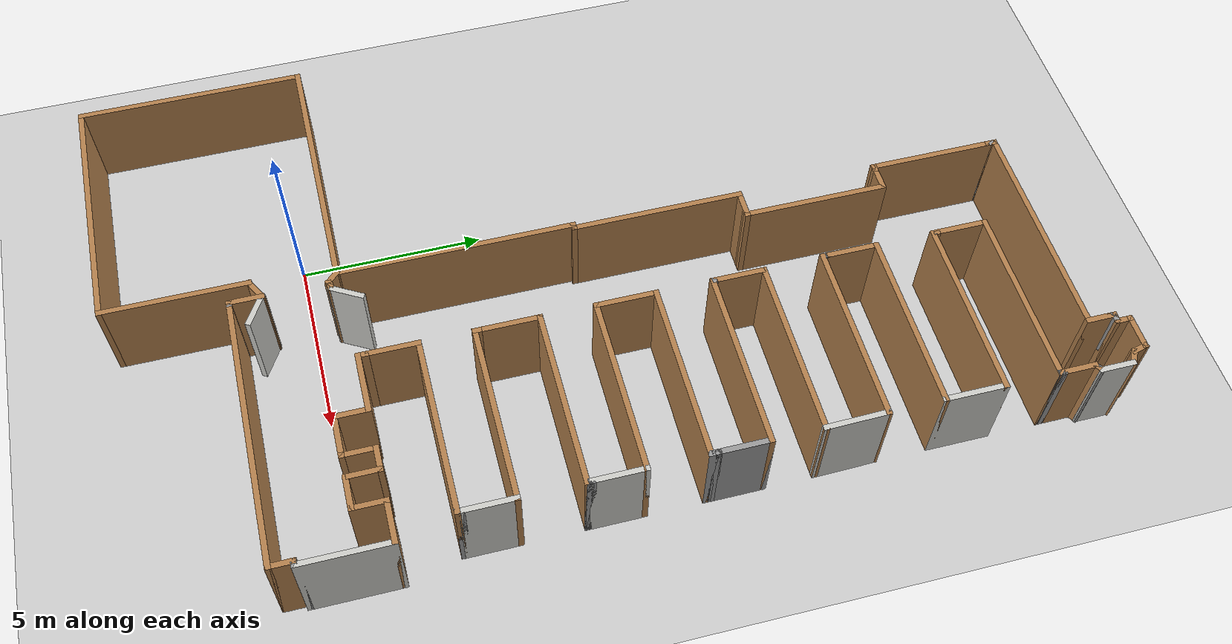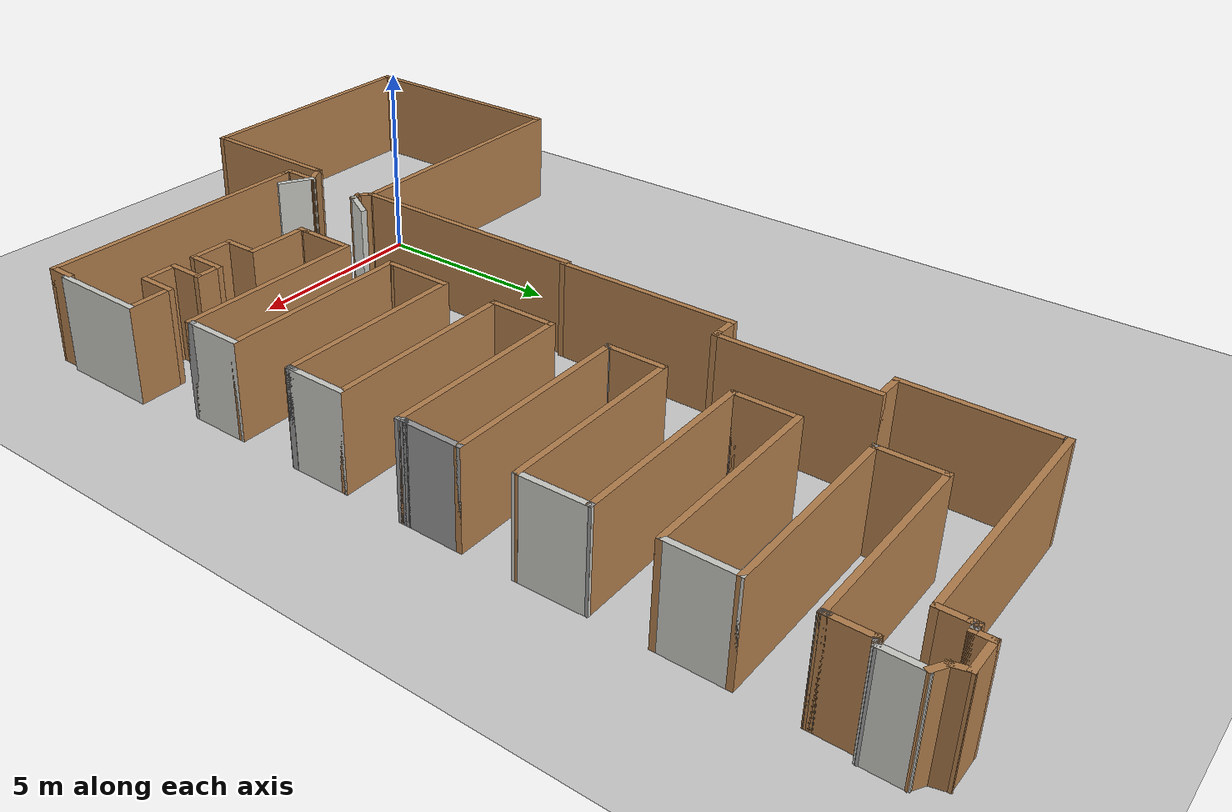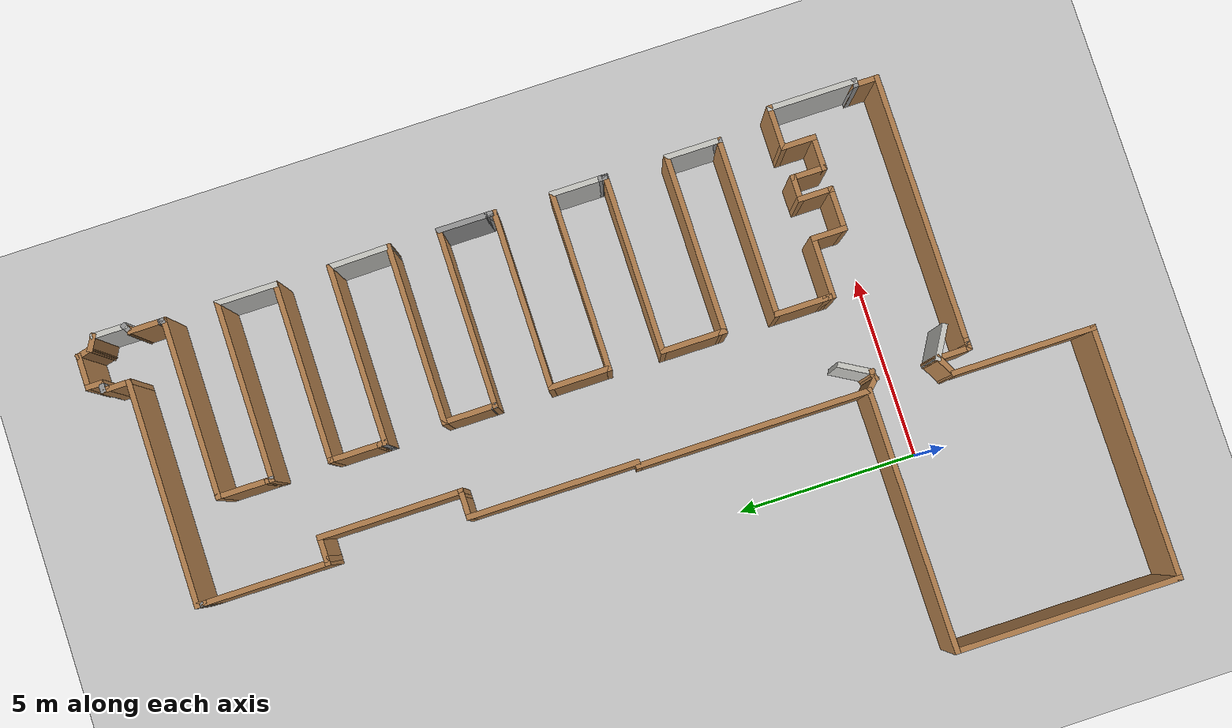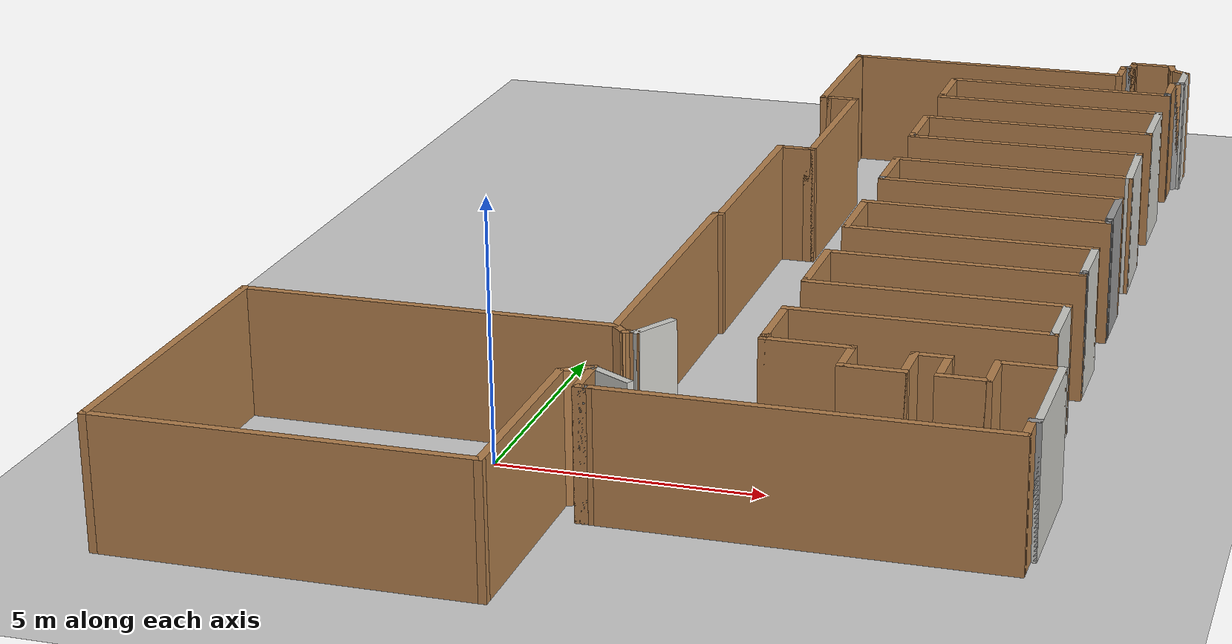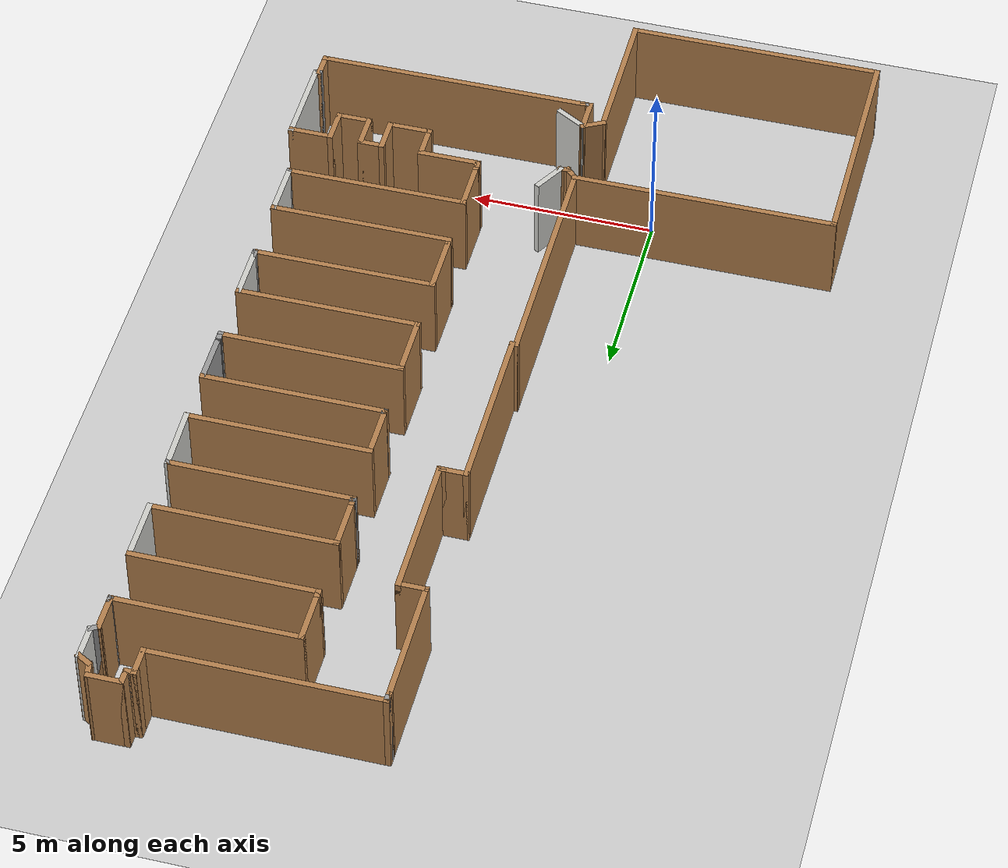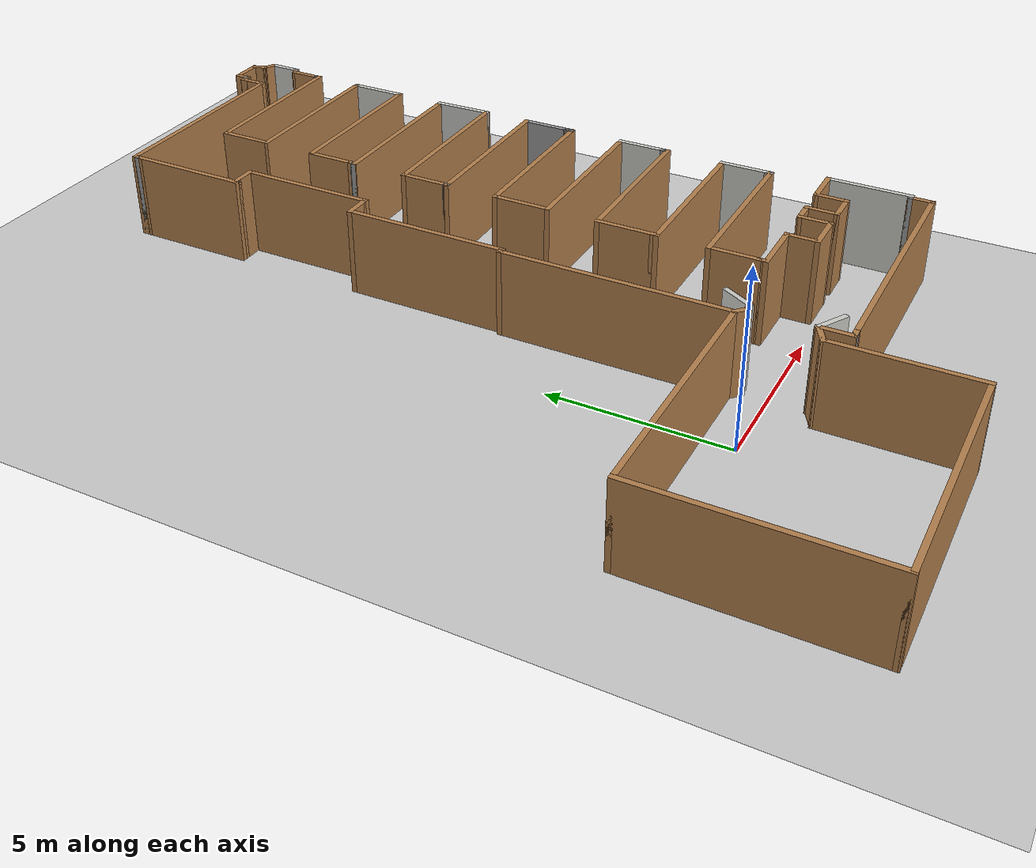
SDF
<sdf version="1.6">
 <world name="default">
  <light name="sun" type="directional">
   <pose>0 0 10 0 -0 0</pose>
   <diffuse>0.8 0.8 0.8 1</diffuse>
   <specular>0.2 0.2 0.2 1</specular>
   <attenuation>
    <range>1000</range>
    <constant>0.9</constant>
    <linear>0.01</linear>
    <quadratic>0.001</quadratic>
   </attenuation>
   <direction>-0.5 0.1 -0.9</direction>
  </light>
  <model name="ground_plane">
   <static>1</static>
   <link name="link">
    <collision name="collision">
     <geometry><plane><normal>0 0 1</normal><size>100 100</size></plane></geometry>
     <surface>
      <contact><collide_bitmask>65535</collide_bitmask></contact>
      <friction><ode><mu>100</mu><mu2>50</mu2></ode></friction>
     </surface>
    </collision>
    <visual name="visual">
     <cast_shadows>0</cast_shadows>
     <geometry><plane><normal>0 0 1</normal><size>100 100</size></plane></geometry>
     <material>
      <script><uri>file://media/materials/scripts/gazebo.material</uri><name>Gazebo/Grey</name></script>
     </material>
    </visual>
   </link>
  </model>
  <gravity>0 0 -9.8</gravity>
  <magnetic_field>6e-06 2.3e-05 -4.2e-05</magnetic_field>
  <atmosphere type="adiabatic"/>
  <physics name="default_physics" default="0" type="ode">
   <max_step_size>0.001</max_step_size>
   <real_time_factor>1</real_time_factor>
   <real_time_update_rate>1000</real_time_update_rate>
  </physics>
  <scene><ambient>0.4 0.4 0.4 1</ambient><background>0.7 0.7 0.7 1</background><shadows>1</shadows></scene>
  <audio><device>default</device></audio>
  <spherical_coordinates>
   <surface_model>EARTH_WGS84</surface_model>
   <latitude_deg>0</latitude_deg>
   <longitude_deg>0</longitude_deg>
   <elevation>0</elevation>
   <heading_deg>0</heading_deg>
  </spherical_coordinates>
  <model name="ecst_lab_v2">
   <pose>2.38151 7.60499 0 0 -0 -1.57079</pose>
   <link name="Wall_1">
    <collision name="Wall_1_Collision">
     <geometry><box><size>5 0.15 2.5</size></box></geometry>
     <pose>0 0 1.25 0 -0 0</pose>
    </collision>
    <visual name="Wall_1_Visual">
     <pose>0 0 1.25 0 -0 0</pose>
     <geometry><box><size>5 0.15 2.5</size></box></geometry>
     <material>
      <script><uri>file://media/materials/scripts/gazebo.material</uri><name>Gazebo/Wood</name></script>
      <ambient>1 1 1 1</ambient>
     </material>
     <meta><layer>0</layer></meta>
    </visual>
    <pose>-4.16301 4.67727 0 0 -0 -1.5708</pose>
   </link>
   <link name="Wall_10">
    <collision name="Wall_10_Collision">
     <geometry><box><size>1.5 0.15 2.5</size></box></geometry>
     <pose>0 0 1.25 0 -0 0</pose>
    </collision>
    <visual name="Wall_10_Visual">
     <pose>0 0 1.25 0 -0 0</pose>
     <geometry><box><size>1.5 0.15 2.5</size></box></geometry>
     <material>
      <script><uri>file://media/materials/scripts/gazebo.material</uri><name>Gazebo/Grey</name></script>
      <ambient>1 1 1 1</ambient>
     </material>
     <meta><layer>0</layer></meta>
    </visual>
    <pose>-2.09801 7.10227 0 0 -0 0</pose>
   </link>
   <link name="Wall_100">
    <collision name="Wall_100_Collision">
     <geometry><box><size>1 0.15 2.5</size></box></geometry>
     <pose>0 0 1.25 0 -0 0</pose>
    </collision>
    <visual name="Wall_100_Visual">
     <pose>0 0 1.25 0 -0 0</pose>
     <geometry><box><size>1 0.15 2.5</size></box></geometry>
     <material>
      <script><uri>file://media/materials/scripts/gazebo.material</uri><name>Gazebo/Wood</name></script>
      <ambient>1 1 1 1</ambient>
     </material>
     <meta><layer>0</layer></meta>
    </visual>
    <pose>-10.8485 7.06822 0 0 -0 0</pose>
   </link>
   <link name="Wall_101">
    <collision name="Wall_101_Collision">
     <geometry><box><size>0.15 0.15 2.5</size></box></geometry>
     <pose>0 0 1.25 0 -0 0</pose>
    </collision>
    <visual name="Wall_101_Visual">
     <pose>0 0 1.25 0 -0 0</pose>
     <geometry><box><size>0.15 0.15 2.5</size></box></geometry>
     <material>
      <script><uri>file://media/materials/scripts/gazebo.material</uri><name>Gazebo/Grey</name></script>
      <ambient>1 1 1 1</ambient>
     </material>
     <meta><layer>0</layer></meta>
    </visual>
    <pose>-10.4235 7.06822 0 0 -0 0</pose>
   </link>
   <link name="Wall_102">
    <collision name="Wall_102_Collision">
     <geometry><box><size>0.16 0.15 2.5</size></box></geometry>
     <pose>0 0 1.25 0 -0 0</pose>
    </collision>
    <visual name="Wall_102_Visual">
     <pose>0 0 1.25 0 -0 0</pose>
     <geometry><box><size>0.16 0.15 2.5</size></box></geometry>
     <material>
      <script><uri>file://media/materials/scripts/gazebo.material</uri><name>Gazebo/Grey</name></script>
      <ambient>1 1 1 1</ambient>
     </material>
     <meta><layer>0</layer></meta>
    </visual>
    <pose>-10.4185 7.06822 0 0 -0 0</pose>
   </link>
   <link name="Wall_103">
    <collision name="Wall_103_Collision">
     <geometry><box><size>0.16 0.15 2.5</size></box></geometry>
     <pose>0 0 1.25 0 -0 0</pose>
    </collision>
    <visual name="Wall_103_Visual">
     <pose>0 0 1.25 0 -0 0</pose>
     <geometry><box><size>0.16 0.15 2.5</size></box></geometry>
     <material>
      <script><uri>file://media/materials/scripts/gazebo.material</uri><name>Gazebo/Grey</name></script>
      <ambient>1 1 1 1</ambient>
     </material>
     <meta><layer>0</layer></meta>
    </visual>
    <pose>-10.4085 7.06822 0 0 -0 0</pose>
   </link>
   <link name="Wall_104">
    <collision name="Wall_104_Collision">
     <geometry><box><size>0.16 0.15 2.5</size></box></geometry>
     <pose>0 0 1.25 0 -0 0</pose>
    </collision>
    <visual name="Wall_104_Visual">
     <pose>0 0 1.25 0 -0 0</pose>
     <geometry><box><size>0.16 0.15 2.5</size></box></geometry>
     <material>
      <script><uri>file://media/materials/scripts/gazebo.material</uri><name>Gazebo/Wood</name></script>
      <ambient>1 1 1 1</ambient>
     </material>
     <meta><layer>0</layer></meta>
    </visual>
    <pose>-10.3985 7.06822 0 0 -0 0</pose>
   </link>
   <link name="Wall_105">
    <collision name="Wall_105_Collision">
     <geometry><box><size>0.16 0.15 2.5</size></box></geometry>
     <pose>0 0 1.25 0 -0 0</pose>
    </collision>
    <visual name="Wall_105_Visual">
     <pose>0 0 1.25 0 -0 0</pose>
     <geometry><box><size>0.16 0.15 2.5</size></box></geometry>
     <material>
      <script><uri>file://media/materials/scripts/gazebo.material</uri><name>Gazebo/Grey</name></script>
      <ambient>1 1 1 1</ambient>
     </material>
     <meta><layer>0</layer></meta>
    </visual>
    <pose>-10.3885 7.06822 0 0 -0 0</pose>
   </link>
   <link name="Wall_106">
    <collision name="Wall_106_Collision">
     <geometry><box><size>0.16 0.15 2.5</size></box></geometry>
     <pose>0 0 1.25 0 -0 0</pose>
    </collision>
    <visual name="Wall_106_Visual">
     <pose>0 0 1.25 0 -0 0</pose>
     <geometry><box><size>0.16 0.15 2.5</size></box></geometry>
     <material>
      <script><uri>file://media/materials/scripts/gazebo.material</uri><name>Gazebo/Wood</name></script>
      <ambient>1 1 1 1</ambient>
     </material>
     <meta><layer>0</layer></meta>
    </visual>
    <pose>-10.3785 7.06822 0 0 -0 0</pose>
   </link>
   <link name="Wall_107">
    <collision name="Wall_107_Collision">
     <geometry><box><size>0.16 0.15 2.5</size></box></geometry>
     <pose>0 0 1.25 0 -0 0</pose>
    </collision>
    <visual name="Wall_107_Visual">
     <pose>0 0 1.25 0 -0 0</pose>
     <geometry><box><size>0.16 0.15 2.5</size></box></geometry>
     <material>
      <script><uri>file://media/materials/scripts/gazebo.material</uri><name>Gazebo/Grey</name></script>
      <ambient>1 1 1 1</ambient>
     </material>
     <meta><layer>0</layer></meta>
    </visual>
    <pose>-10.3685 7.06822 0 0 -0 0</pose>
   </link>
   <link name="Wall_108">
    <collision name="Wall_108_Collision">
     <geometry><box><size>0.16 0.15 2.5</size></box></geometry>
     <pose>0 0 1.25 0 -0 0</pose>
    </collision>
    <visual name="Wall_108_Visual">
     <pose>0 0 1.25 0 -0 0</pose>
     <geometry><box><size>0.16 0.15 2.5</size></box></geometry>
     <material>
      <script><uri>file://media/materials/scripts/gazebo.material</uri><name>Gazebo/Grey</name></script>
      <ambient>1 1 1 1</ambient>
     </material>
     <meta><layer>0</layer></meta>
    </visual>
    <pose>-10.3685 7.06822 0 0 -0 3.14159</pose>
   </link>
   <link name="Wall_109">
    <collision name="Wall_109_Collision">
     <geometry><box><size>0.16 0.15 2.5</size></box></geometry>
     <pose>0 0 1.25 0 -0 0</pose>
    </collision>
    <visual name="Wall_109_Visual">
     <pose>0 0 1.25 0 -0 0</pose>
     <geometry><box><size>0.16 0.15 2.5</size></box></geometry>
     <material>
      <script><uri>file://media/materials/scripts/gazebo.material</uri><name>Gazebo/Grey</name></script>
      <ambient>1 1 1 1</ambient>
     </material>
     <meta><layer>0</layer></meta>
    </visual>
    <pose>-10.3685 7.06822 0 0 -0 0</pose>
   </link>
   <link name="Wall_11">
    <collision name="Wall_11_Collision">
     <geometry><box><size>0.15 0.15 2.5</size></box></geometry>
     <pose>0 0 1.25 0 -0 0</pose>
    </collision>
    <visual name="Wall_11_Visual">
     <pose>0 0 1.25 0 -0 0</pose>
     <geometry><box><size>0.15 0.15 2.5</size></box></geometry>
     <material>
      <script><uri>file://media/materials/scripts/gazebo.material</uri><name>Gazebo/Grey</name></script>
      <ambient>1 1 1 1</ambient>
     </material>
     <meta><layer>0</layer></meta>
    </visual>
    <pose>-1.42301 7.10227 0 0 -0 0</pose>
   </link>
   <link name="Wall_110">
    <collision name="Wall_110_Collision">
     <geometry><box><size>0.16 0.15 2.5</size></box></geometry>
     <pose>0 0 1.25 0 -0 0</pose>
    </collision>
    <visual name="Wall_110_Visual">
     <pose>0 0 1.25 0 -0 0</pose>
     <geometry><box><size>0.16 0.15 2.5</size></box></geometry>
     <material>
      <script><uri>file://media/materials/scripts/gazebo.material</uri><name>Gazebo/Grey</name></script>
      <ambient>1 1 1 1</ambient>
     </material>
     <meta><layer>0</layer></meta>
    </visual>
    <pose>-10.3685 7.06822 0 0 -0 3.14159</pose>
   </link>
   <link name="Wall_111">
    <collision name="Wall_111_Collision">
     <geometry><box><size>0.16 0.15 2.5</size></box></geometry>
     <pose>0 0 1.25 0 -0 0</pose>
    </collision>
    <visual name="Wall_111_Visual">
     <pose>0 0 1.25 0 -0 0</pose>
     <geometry><box><size>0.16 0.15 2.5</size></box></geometry>
     <material>
      <script><uri>file://media/materials/scripts/gazebo.material</uri><name>Gazebo/Grey</name></script>
      <ambient>1 1 1 1</ambient>
     </material>
     <meta><layer>0</layer></meta>
    </visual>
    <pose>-10.3685 7.06822 0 0 -0 0</pose>
   </link>
   <link name="Wall_112">
    <collision name="Wall_112_Collision">
     <geometry><box><size>0.16 0.15 2.5</size></box></geometry>
     <pose>0 0 1.25 0 -0 0</pose>
    </collision>
    <visual name="Wall_112_Visual">
     <pose>0 0 1.25 0 -0 0</pose>
     <geometry><box><size>0.16 0.15 2.5</size></box></geometry>
     <material>
      <script><uri>file://media/materials/scripts/gazebo.material</uri><name>Gazebo/Grey</name></script>
      <ambient>1 1 1 1</ambient>
     </material>
     <meta><layer>0</layer></meta>
    </visual>
    <pose>-10.3685 7.06822 0 0 -0 3.14159</pose>
   </link>
   <link name="Wall_113">
    <collision name="Wall_113_Collision">
     <geometry><box><size>0.16 0.15 2.5</size></box></geometry>
     <pose>0 0 1.25 0 -0 0</pose>
    </collision>
    <visual name="Wall_113_Visual">
     <pose>0 0 1.25 0 -0 0</pose>
     <geometry><box><size>0.16 0.15 2.5</size></box></geometry>
     <material>
      <script><uri>file://media/materials/scripts/gazebo.material</uri><name>Gazebo/Grey</name></script>
      <ambient>1 1 1 1</ambient>
     </material>
     <meta><layer>0</layer></meta>
    </visual>
    <pose>-10.3685 7.06822 0 0 -0 0</pose>
   </link>
   <link name="Wall_114">
    <collision name="Wall_114_Collision">
     <geometry><box><size>0.16 0.15 2.5</size></box></geometry>
     <pose>0 0 1.25 0 -0 0</pose>
    </collision>
    <visual name="Wall_114_Visual">
     <pose>0 0 1.25 0 -0 0</pose>
     <geometry><box><size>0.16 0.15 2.5</size></box></geometry>
     <material>
      <script><uri>file://media/materials/scripts/gazebo.material</uri><name>Gazebo/Grey</name></script>
      <ambient>1 1 1 1</ambient>
     </material>
     <meta><layer>0</layer></meta>
    </visual>
    <pose>-10.3685 7.06822 0 0 -0 3.14159</pose>
   </link>
   <link name="Wall_115">
    <collision name="Wall_115_Collision">
     <geometry><box><size>0.16 0.15 2.5</size></box></geometry>
     <pose>0 0 1.25 0 -0 0</pose>
    </collision>
    <visual name="Wall_115_Visual">
     <pose>0 0 1.25 0 -0 0</pose>
     <geometry><box><size>0.16 0.15 2.5</size></box></geometry>
     <material>
      <script><uri>file://media/materials/scripts/gazebo.material</uri><name>Gazebo/Wood</name></script>
      <ambient>1 1 1 1</ambient>
     </material>
     <meta><layer>0</layer></meta>
    </visual>
    <pose>-10.3685 7.06822 0 0 -0 0</pose>
   </link>
   <link name="Wall_116">
    <collision name="Wall_116_Collision">
     <geometry><box><size>0.16 0.15 2.5</size></box></geometry>
     <pose>0 0 1.25 0 -0 0</pose>
    </collision>
    <visual name="Wall_116_Visual">
     <pose>0 0 1.25 0 -0 0</pose>
     <geometry><box><size>0.16 0.15 2.5</size></box></geometry>
     <material>
      <script><uri>file://media/materials/scripts/gazebo.material</uri><name>Gazebo/Grey</name></script>
      <ambient>1 1 1 1</ambient>
     </material>
     <meta><layer>0</layer></meta>
    </visual>
    <pose>-10.3585 7.06822 0 0 -0 0</pose>
   </link>
   <link name="Wall_117">
    <collision name="Wall_117_Collision">
     <geometry><box><size>0.16 0.15 2.5</size></box></geometry>
     <pose>0 0 1.25 0 -0 0</pose>
    </collision>
    <visual name="Wall_117_Visual">
     <pose>0 0 1.25 0 -0 0</pose>
     <geometry><box><size>0.16 0.15 2.5</size></box></geometry>
     <material>
      <script><uri>file://media/materials/scripts/gazebo.material</uri><name>Gazebo/Wood</name></script>
      <ambient>1 1 1 1</ambient>
     </material>
     <meta><layer>0</layer></meta>
    </visual>
    <pose>-10.3485 7.06822 0 0 -0 0</pose>
   </link>
   <link name="Wall_118">
    <collision name="Wall_118_Collision">
     <geometry><box><size>5 0.15 2.5</size></box></geometry>
     <pose>0 0 1.25 0 -0 0</pose>
    </collision>
    <visual name="Wall_118_Visual">
     <pose>0 0 1.25 0 -0 0</pose>
     <geometry><box><size>5 0.15 2.5</size></box></geometry>
     <material>
      <script><uri>file://media/materials/scripts/gazebo.material</uri><name>Gazebo/Wood</name></script>
      <ambient>1 1 1 1</ambient>
     </material>
     <meta><layer>0</layer></meta>
    </visual>
    <pose>-10.3435 4.64322 0 0 -0 -1.5708</pose>
   </link>
   <link name="Wall_119">
    <collision name="Wall_119_Collision">
     <geometry><box><size>1.5 0.15 2.5</size></box></geometry>
     <pose>0 0 1.25 0 -0 0</pose>
    </collision>
    <visual name="Wall_119_Visual">
     <pose>0 0 1.25 0 -0 0</pose>
     <geometry><box><size>1.5 0.15 2.5</size></box></geometry>
     <material>
      <script><uri>file://media/materials/scripts/gazebo.material</uri><name>Gazebo/Wood</name></script>
      <ambient>1 1 1 1</ambient>
     </material>
     <meta><layer>0</layer></meta>
    </visual>
    <pose>-9.6685 2.21822 0 0 -0 0</pose>
   </link>
   <link name="Wall_12">
    <collision name="Wall_12_Collision">
     <geometry><box><size>0.16 0.15 2.5</size></box></geometry>
     <pose>0 0 1.25 0 -0 0</pose>
    </collision>
    <visual name="Wall_12_Visual">
     <pose>0 0 1.25 0 -0 0</pose>
     <geometry><box><size>0.16 0.15 2.5</size></box></geometry>
     <material>
      <script><uri>file://media/materials/scripts/gazebo.material</uri><name>Gazebo/Grey</name></script>
      <ambient>1 1 1 1</ambient>
     </material>
     <meta><layer>0</layer></meta>
    </visual>
    <pose>-1.41801 7.10227 0 0 -0 0</pose>
   </link>
   <link name="Wall_120">
    <collision name="Wall_120_Collision">
     <geometry><box><size>0.25 0.15 2.5</size></box></geometry>
     <pose>0 0 1.25 0 -0 0</pose>
    </collision>
    <visual name="Wall_120_Visual">
     <pose>0 0 1.25 0 -0 0</pose>
     <geometry><box><size>0.25 0.15 2.5</size></box></geometry>
     <material>
      <script><uri>file://media/materials/scripts/gazebo.material</uri><name>Gazebo/Wood</name></script>
      <ambient>1 1 1 1</ambient>
     </material>
     <meta><layer>0</layer></meta>
    </visual>
    <pose>-8.9435 2.21822 0 0 -0 0</pose>
   </link>
   <link name="Wall_121">
    <collision name="Wall_121_Collision">
     <geometry><box><size>0.15 0.15 2.5</size></box></geometry>
     <pose>0 0 1.25 0 -0 0</pose>
    </collision>
    <visual name="Wall_121_Visual">
     <pose>0 0 1.25 0 -0 0</pose>
     <geometry><box><size>0.15 0.15 2.5</size></box></geometry>
     <material>
      <script><uri>file://media/materials/scripts/gazebo.material</uri><name>Gazebo/Grey</name></script>
      <ambient>1 1 1 1</ambient>
     </material>
     <meta><layer>0</layer></meta>
    </visual>
    <pose>-8.8935 2.21822 0 0 -0 0</pose>
   </link>
   <link name="Wall_122">
    <collision name="Wall_122_Collision">
     <geometry><box><size>0.16 0.15 2.5</size></box></geometry>
     <pose>0 0 1.25 0 -0 0</pose>
    </collision>
    <visual name="Wall_122_Visual">
     <pose>0 0 1.25 0 -0 0</pose>
     <geometry><box><size>0.16 0.15 2.5</size></box></geometry>
     <material>
      <script><uri>file://media/materials/scripts/gazebo.material</uri><name>Gazebo/Wood</name></script>
      <ambient>1 1 1 1</ambient>
     </material>
     <meta><layer>0</layer></meta>
    </visual>
    <pose>-8.8885 2.21822 0 0 -0 0</pose>
   </link>
   <link name="Wall_123">
    <collision name="Wall_123_Collision">
     <geometry><box><size>5 0.15 2.5</size></box></geometry>
     <pose>0 0 1.25 0 -0 0</pose>
    </collision>
    <visual name="Wall_123_Visual">
     <pose>0 0 1.25 0 -0 0</pose>
     <geometry><box><size>5 0.15 2.5</size></box></geometry>
     <material>
      <script><uri>file://media/materials/scripts/gazebo.material</uri><name>Gazebo/Wood</name></script>
      <ambient>1 1 1 1</ambient>
     </material>
     <meta><layer>0</layer></meta>
    </visual>
    <pose>-8.8835 4.64322 0 0 -0 1.5708</pose>
   </link>
   <link name="Wall_124">
    <collision name="Wall_124_Collision">
     <geometry><box><size>1.75 0.15 2.5</size></box></geometry>
     <pose>0 0 1.25 0 -0 0</pose>
    </collision>
    <visual name="Wall_124_Visual">
     <pose>0 0 1.25 0 -0 0</pose>
     <geometry><box><size>1.75 0.15 2.5</size></box></geometry>
     <material>
      <script><uri>file://media/materials/scripts/gazebo.material</uri><name>Gazebo/CeilingTiled</name></script>
      <ambient>1 1 1 1</ambient>
     </material>
     <meta><layer>0</layer></meta>
    </visual>
    <pose>-8.0835 7.06822 0 0 -0 0</pose>
   </link>
   <link name="Wall_125">
    <collision name="Wall_125_Collision">
     <geometry><box><size>5 0.15 2.5</size></box></geometry>
     <pose>0 0 1.25 0 -0 0</pose>
    </collision>
    <visual name="Wall_125_Visual">
     <pose>0 0 1.25 0 -0 0</pose>
     <geometry><box><size>5 0.15 2.5</size></box></geometry>
     <material>
      <script><uri>file://media/materials/scripts/gazebo.material</uri><name>Gazebo/Wood</name></script>
      <ambient>1 1 1 1</ambient>
     </material>
     <meta><layer>0</layer></meta>
    </visual>
    <pose>-7.2835 4.64322 0 0 -0 -1.5708</pose>
   </link>
   <link name="Wall_126">
    <collision name="Wall_126_Collision">
     <geometry><box><size>1.5 0.15 2.5</size></box></geometry>
     <pose>0 0 1.25 0 -0 0</pose>
    </collision>
    <visual name="Wall_126_Visual">
     <pose>0 0 1.25 0 -0 0</pose>
     <geometry><box><size>1.5 0.15 2.5</size></box></geometry>
     <material>
      <script><uri>file://media/materials/scripts/gazebo.material</uri><name>Gazebo/Wood</name></script>
      <ambient>1 1 1 1</ambient>
     </material>
     <meta><layer>0</layer></meta>
    </visual>
    <pose>-6.6085 2.21822 0 0 -0 0</pose>
   </link>
   <link name="Wall_127">
    <collision name="Wall_127_Collision">
     <geometry><box><size>0.25 0.15 2.5</size></box></geometry>
     <pose>0 0 1.25 0 -0 0</pose>
    </collision>
    <visual name="Wall_127_Visual">
     <pose>0 0 1.25 0 -0 0</pose>
     <geometry><box><size>0.25 0.15 2.5</size></box></geometry>
     <material>
      <script><uri>file://media/materials/scripts/gazebo.material</uri><name>Gazebo/Wood</name></script>
      <ambient>1 1 1 1</ambient>
     </material>
     <meta><layer>0</layer></meta>
    </visual>
    <pose>-5.8835 2.21822 0 0 -0 0</pose>
   </link>
   <link name="Wall_128">
    <collision name="Wall_128_Collision">
     <geometry><box><size>0.15 0.15 2.5</size></box></geometry>
     <pose>0 0 1.25 0 -0 0</pose>
    </collision>
    <visual name="Wall_128_Visual">
     <pose>0 0 1.25 0 -0 0</pose>
     <geometry><box><size>0.15 0.15 2.5</size></box></geometry>
     <material>
      <script><uri>file://media/materials/scripts/gazebo.material</uri><name>Gazebo/Grey</name></script>
      <ambient>1 1 1 1</ambient>
     </material>
     <meta><layer>0</layer></meta>
    </visual>
    <pose>-5.8335 2.21822 0 0 -0 0</pose>
   </link>
   <link name="Wall_129">
    <collision name="Wall_129_Collision">
     <geometry><box><size>0.16 0.15 2.5</size></box></geometry>
     <pose>0 0 1.25 0 -0 0</pose>
    </collision>
    <visual name="Wall_129_Visual">
     <pose>0 0 1.25 0 -0 0</pose>
     <geometry><box><size>0.16 0.15 2.5</size></box></geometry>
     <material>
      <script><uri>file://media/materials/scripts/gazebo.material</uri><name>Gazebo/Wood</name></script>
      <ambient>1 1 1 1</ambient>
     </material>
     <meta><layer>0</layer></meta>
    </visual>
    <pose>-5.8285 2.21822 0 0 -0 0</pose>
   </link>
   <link name="Wall_13">
    <collision name="Wall_13_Collision">
     <geometry><box><size>0.16 0.15 2.5</size></box></geometry>
     <pose>0 0 1.25 0 -0 0</pose>
    </collision>
    <visual name="Wall_13_Visual">
     <pose>0 0 1.25 0 -0 0</pose>
     <geometry><box><size>0.16 0.15 2.5</size></box></geometry>
     <material>
      <script><uri>file://media/materials/scripts/gazebo.material</uri><name>Gazebo/Grey</name></script>
      <ambient>1 1 1 1</ambient>
     </material>
     <meta><layer>0</layer></meta>
    </visual>
    <pose>-1.40801 7.10227 0 0 -0 0</pose>
   </link>
   <link name="Wall_130">
    <collision name="Wall_130_Collision">
     <geometry><box><size>0.16 0.15 2.5</size></box></geometry>
     <pose>0 0 1.25 0 -0 0</pose>
    </collision>
    <visual name="Wall_130_Visual">
     <pose>0 0 1.25 0 -0 0</pose>
     <geometry><box><size>0.16 0.15 2.5</size></box></geometry>
     <material>
      <script><uri>file://media/materials/scripts/gazebo.material</uri><name>Gazebo/Grey</name></script>
      <ambient>1 1 1 1</ambient>
     </material>
     <meta><layer>0</layer></meta>
    </visual>
    <pose>-5.8185 2.21822 0 0 -0 0</pose>
   </link>
   <link name="Wall_131">
    <collision name="Wall_131_Collision">
     <geometry><box><size>0.16 0.15 2.5</size></box></geometry>
     <pose>0 0 1.25 0 -0 0</pose>
    </collision>
    <visual name="Wall_131_Visual">
     <pose>0 0 1.25 0 -0 0</pose>
     <geometry><box><size>0.16 0.15 2.5</size></box></geometry>
     <material>
      <script><uri>file://media/materials/scripts/gazebo.material</uri><name>Gazebo/Grey</name></script>
      <ambient>1 1 1 1</ambient>
     </material>
     <meta><layer>0</layer></meta>
    </visual>
    <pose>-5.8085 2.21822 0 0 -0 0</pose>
   </link>
   <link name="Wall_132">
    <collision name="Wall_132_Collision">
     <geometry><box><size>0.16 0.15 2.5</size></box></geometry>
     <pose>0 0 1.25 0 -0 0</pose>
    </collision>
    <visual name="Wall_132_Visual">
     <pose>0 0 1.25 0 -0 0</pose>
     <geometry><box><size>0.16 0.15 2.5</size></box></geometry>
     <material>
      <script><uri>file://media/materials/scripts/gazebo.material</uri><name>Gazebo/Wood</name></script>
      <ambient>1 1 1 1</ambient>
     </material>
     <meta><layer>0</layer></meta>
    </visual>
    <pose>-5.7985 2.21822 0 0 -0 0</pose>
   </link>
   <link name="Wall_133">
    <collision name="Wall_133_Collision">
     <geometry><box><size>5 0.15 2.5</size></box></geometry>
     <pose>0 0 1.25 0 -0 0</pose>
    </collision>
    <visual name="Wall_133_Visual">
     <pose>0 0 1.25 0 -0 0</pose>
     <geometry><box><size>5 0.15 2.5</size></box></geometry>
     <material>
      <script><uri>file://media/materials/scripts/gazebo.material</uri><name>Gazebo/Wood</name></script>
      <ambient>1 1 1 1</ambient>
     </material>
     <meta><layer>0</layer></meta>
    </visual>
    <pose>-5.7935 4.64322 0 0 -0 1.5708</pose>
   </link>
   <link name="Wall_134">
    <collision name="Wall_134_Collision">
     <geometry><box><size>0.15 0.15 2.5</size></box></geometry>
     <pose>0 0 1.25 0 -0 0</pose>
    </collision>
    <visual name="Wall_134_Visual">
     <pose>0 0 1.25 0 -0 0</pose>
     <geometry><box><size>0.15 0.15 2.5</size></box></geometry>
     <material>
      <script><uri>file://media/materials/scripts/gazebo.material</uri><name>Gazebo/Grey</name></script>
      <ambient>1 1 1 1</ambient>
     </material>
     <meta><layer>0</layer></meta>
    </visual>
    <pose>-5.7935 7.06822 0 0 -0 0</pose>
   </link>
   <link name="Wall_135">
    <collision name="Wall_135_Collision">
     <geometry><box><size>0.15 0.15 2.5</size></box></geometry>
     <pose>0 0 1.25 0 -0 0</pose>
    </collision>
    <visual name="Wall_135_Visual">
     <pose>0 0 1.25 0 -0 0</pose>
     <geometry><box><size>0.15 0.15 2.5</size></box></geometry>
     <material>
      <script><uri>file://media/materials/scripts/gazebo.material</uri><name>Gazebo/Grey</name></script>
      <ambient>1 1 1 1</ambient>
     </material>
     <meta><layer>0</layer></meta>
    </visual>
    <pose>-5.7935 7.06822 0 0 -0 0</pose>
   </link>
   <link name="Wall_136">
    <collision name="Wall_136_Collision">
     <geometry><box><size>0.15 0.15 2.5</size></box></geometry>
     <pose>0 0 1.25 0 -0 0</pose>
    </collision>
    <visual name="Wall_136_Visual">
     <pose>0 0 1.25 0 -0 0</pose>
     <geometry><box><size>0.15 0.15 2.5</size></box></geometry>
     <material>
      <script><uri>file://media/materials/scripts/gazebo.material</uri><name>Gazebo/Grey</name></script>
      <ambient>1 1 1 1</ambient>
     </material>
     <meta><layer>0</layer></meta>
    </visual>
    <pose>-5.7935 7.06822 0 0 -0 0</pose>
   </link>
   <link name="Wall_137">
    <collision name="Wall_137_Collision">
     <geometry><box><size>0.15 0.15 2.5</size></box></geometry>
     <pose>0 0 1.25 0 -0 0</pose>
    </collision>
    <visual name="Wall_137_Visual">
     <pose>0 0 1.25 0 -0 0</pose>
     <geometry><box><size>0.15 0.15 2.5</size></box></geometry>
     <material>
      <script><uri>file://media/materials/scripts/gazebo.material</uri><name>Gazebo/Grey</name></script>
      <ambient>1 1 1 1</ambient>
     </material>
     <meta><layer>0</layer></meta>
    </visual>
    <pose>-5.7935 7.06822 0 0 -0 0</pose>
   </link>
   <link name="Wall_138">
    <collision name="Wall_138_Collision">
     <geometry><box><size>1.78084 0.15 2.5</size></box></geometry>
     <pose>0 0 1.25 0 -0 0</pose>
    </collision>
    <visual name="Wall_138_Visual">
     <pose>0 0 1.25 0 -0 0</pose>
     <geometry><box><size>1.78084 0.15 2.5</size></box></geometry>
     <material>
      <script><uri>file://media/materials/scripts/gazebo.material</uri><name>Gazebo/CeilingTiled</name></script>
      <ambient>1 1 1 1</ambient>
     </material>
     <meta><layer>0</layer></meta>
    </visual>
    <pose>-4.97826 7.08524 0 0 -0 0.020886</pose>
   </link>
   <link name="Wall_14">
    <collision name="Wall_14_Collision">
     <geometry><box><size>0.16 0.15 2.5</size></box></geometry>
     <pose>0 0 1.25 0 -0 0</pose>
    </collision>
    <visual name="Wall_14_Visual">
     <pose>0 0 1.25 0 -0 0</pose>
     <geometry><box><size>0.16 0.15 2.5</size></box></geometry>
     <material>
      <script><uri>file://media/materials/scripts/gazebo.material</uri><name>Gazebo/Grey</name></script>
      <ambient>1 1 1 1</ambient>
     </material>
     <meta><layer>0</layer></meta>
    </visual>
    <pose>-1.39801 7.10227 0 0 -0 0</pose>
   </link>
   <link name="Wall_15">
    <collision name="Wall_15_Collision">
     <geometry><box><size>0.16 0.15 2.5</size></box></geometry>
     <pose>0 0 1.25 0 -0 0</pose>
    </collision>
    <visual name="Wall_15_Visual">
     <pose>0 0 1.25 0 -0 0</pose>
     <geometry><box><size>0.16 0.15 2.5</size></box></geometry>
     <material>
      <script><uri>file://media/materials/scripts/gazebo.material</uri><name>Gazebo/Grey</name></script>
      <ambient>1 1 1 1</ambient>
     </material>
     <meta><layer>0</layer></meta>
    </visual>
    <pose>-1.38801 7.10227 0 0 -0 0</pose>
   </link>
   <link name="Wall_16">
    <collision name="Wall_16_Collision">
     <geometry><box><size>0.16 0.15 2.5</size></box></geometry>
     <pose>0 0 1.25 0 -0 0</pose>
    </collision>
    <visual name="Wall_16_Visual">
     <pose>0 0 1.25 0 -0 0</pose>
     <geometry><box><size>0.16 0.15 2.5</size></box></geometry>
     <material>
      <script><uri>file://media/materials/scripts/gazebo.material</uri><name>Gazebo/Grey</name></script>
      <ambient>1 1 1 1</ambient>
     </material>
     <meta><layer>0</layer></meta>
    </visual>
    <pose>-1.37801 7.10227 0 0 -0 0</pose>
   </link>
   <link name="Wall_17">
    <collision name="Wall_17_Collision">
     <geometry><box><size>0.16 0.15 2.5</size></box></geometry>
     <pose>0 0 1.25 0 -0 0</pose>
    </collision>
    <visual name="Wall_17_Visual">
     <pose>0 0 1.25 0 -0 0</pose>
     <geometry><box><size>0.16 0.15 2.5</size></box></geometry>
     <material>
      <script><uri>file://media/materials/scripts/gazebo.material</uri><name>Gazebo/Grey</name></script>
      <ambient>1 1 1 1</ambient>
     </material>
     <meta><layer>0</layer></meta>
    </visual>
    <pose>-1.36801 7.10227 0 0 -0 0</pose>
   </link>
   <link name="Wall_18">
    <collision name="Wall_18_Collision">
     <geometry><box><size>0.16 0.15 2.5</size></box></geometry>
     <pose>0 0 1.25 0 -0 0</pose>
    </collision>
    <visual name="Wall_18_Visual">
     <pose>0 0 1.25 0 -0 0</pose>
     <geometry><box><size>0.16 0.15 2.5</size></box></geometry>
     <material>
      <script><uri>file://media/materials/scripts/gazebo.material</uri><name>Gazebo/Grey</name></script>
      <ambient>1 1 1 1</ambient>
     </material>
     <meta><layer>0</layer></meta>
    </visual>
    <pose>-1.35801 7.10227 0 0 -0 0</pose>
   </link>
   <link name="Wall_19">
    <collision name="Wall_19_Collision">
     <geometry><box><size>0.16 0.15 2.5</size></box></geometry>
     <pose>0 0 1.25 0 -0 0</pose>
    </collision>
    <visual name="Wall_19_Visual">
     <pose>0 0 1.25 0 -0 0</pose>
     <geometry><box><size>0.16 0.15 2.5</size></box></geometry>
     <material>
      <script><uri>file://media/materials/scripts/gazebo.material</uri><name>Gazebo/Grey</name></script>
      <ambient>1 1 1 1</ambient>
     </material>
     <meta><layer>0</layer></meta>
    </visual>
    <pose>-1.34801 7.10227 0 0 -0 0</pose>
   </link>
   <link name="Wall_2">
    <collision name="Wall_2_Collision">
     <geometry><box><size>1.5 0.15 2.5</size></box></geometry>
     <pose>0 0 1.25 0 -0 0</pose>
    </collision>
    <visual name="Wall_2_Visual">
     <pose>0 0 1.25 0 -0 0</pose>
     <geometry><box><size>1.5 0.15 2.5</size></box></geometry>
     <material>
      <script><uri>file://media/materials/scripts/gazebo.material</uri><name>Gazebo/Wood</name></script>
      <ambient>1 1 1 1</ambient>
     </material>
     <meta><layer>0</layer></meta>
    </visual>
    <pose>-3.48801 2.25228 0 0 -0 0</pose>
   </link>
   <link name="Wall_20">
    <collision name="Wall_20_Collision">
     <geometry><box><size>0.25 0.15 2.5</size></box></geometry>
     <pose>0 0 1.25 0 -0 0</pose>
    </collision>
    <visual name="Wall_20_Visual">
     <pose>0 0 1.25 0 -0 0</pose>
     <geometry><box><size>0.25 0.15 2.5</size></box></geometry>
     <material>
      <script><uri>file://media/materials/scripts/gazebo.material</uri><name>Gazebo/Grey</name></script>
      <ambient>1 1 1 1</ambient>
     </material>
     <meta><layer>0</layer></meta>
    </visual>
    <pose>-1.29301 7.10227 0 0 -0 0</pose>
   </link>
   <link name="Wall_21">
    <collision name="Wall_21_Collision">
     <geometry><box><size>5 0.15 2.5</size></box></geometry>
     <pose>0 0 1.25 0 -0 0</pose>
    </collision>
    <visual name="Wall_21_Visual">
     <pose>0 0 1.25 0 -0 0</pose>
     <geometry><box><size>5 0.15 2.5</size></box></geometry>
     <material>
      <script><uri>file://media/materials/scripts/gazebo.material</uri><name>Gazebo/Wood</name></script>
      <ambient>1 1 1 1</ambient>
     </material>
     <meta><layer>0</layer></meta>
    </visual>
    <pose>-1.24301 4.67727 0 0 -0 -1.5708</pose>
   </link>
   <link name="Wall_22">
    <collision name="Wall_22_Collision">
     <geometry><box><size>1.75 0.15 2.5</size></box></geometry>
     <pose>0 0 1.25 0 -0 0</pose>
    </collision>
    <visual name="Wall_22_Visual">
     <pose>0 0 1.25 0 -0 0</pose>
     <geometry><box><size>1.75 0.15 2.5</size></box></geometry>
     <material>
      <script><uri>file://media/materials/scripts/gazebo.material</uri><name>Gazebo/Wood</name></script>
      <ambient>1 1 1 1</ambient>
     </material>
     <meta><layer>0</layer></meta>
    </visual>
    <pose>-0.443013 2.25228 0 0 -0 0</pose>
   </link>
   <link name="Wall_23">
    <collision name="Wall_23_Collision">
     <geometry><box><size>5 0.15 2.5</size></box></geometry>
     <pose>0 0 1.25 0 -0 0</pose>
    </collision>
    <visual name="Wall_23_Visual">
     <pose>0 0 1.25 0 -0 0</pose>
     <geometry><box><size>5 0.15 2.5</size></box></geometry>
     <material>
      <script><uri>file://media/materials/scripts/gazebo.material</uri><name>Gazebo/Wood</name></script>
      <ambient>1 1 1 1</ambient>
     </material>
     <meta><layer>0</layer></meta>
    </visual>
    <pose>0.356987 4.67727 0 0 -0 1.5708</pose>
   </link>
   <link name="Wall_24">
    <collision name="Wall_24_Collision">
     <geometry><box><size>1.5 0.15 2.5</size></box></geometry>
     <pose>0 0 1.25 0 -0 0</pose>
    </collision>
    <visual name="Wall_24_Visual">
     <pose>0 0 1.25 0 -0 0</pose>
     <geometry><box><size>1.5 0.15 2.5</size></box></geometry>
     <material>
      <script><uri>file://media/materials/scripts/gazebo.material</uri><name>Gazebo/CeilingTiled</name></script>
      <ambient>1 1 1 1</ambient>
     </material>
     <meta><layer>0</layer></meta>
    </visual>
    <pose>1.03199 7.10227 0 0 -0 0</pose>
   </link>
   <link name="Wall_25">
    <collision name="Wall_25_Collision">
     <geometry><box><size>0.25 0.15 2.5</size></box></geometry>
     <pose>0 0 1.25 0 -0 0</pose>
    </collision>
    <visual name="Wall_25_Visual">
     <pose>0 0 1.25 0 -0 0</pose>
     <geometry><box><size>0.25 0.15 2.5</size></box></geometry>
     <material>
      <script><uri>file://media/materials/scripts/gazebo.material</uri><name>Gazebo/Grey</name></script>
      <ambient>1 1 1 1</ambient>
     </material>
     <meta><layer>0</layer></meta>
    </visual>
    <pose>1.75699 7.10227 0 0 -0 0</pose>
   </link>
   <link name="Wall_26">
    <collision name="Wall_26_Collision">
     <geometry><box><size>0.15 0.15 2.5</size></box></geometry>
     <pose>0 0 1.25 0 -0 0</pose>
    </collision>
    <visual name="Wall_26_Visual">
     <pose>0 0 1.25 0 -0 0</pose>
     <geometry><box><size>0.15 0.15 2.5</size></box></geometry>
     <material>
      <script><uri>file://media/materials/scripts/gazebo.material</uri><name>Gazebo/Grey</name></script>
      <ambient>1 1 1 1</ambient>
     </material>
     <meta><layer>0</layer></meta>
    </visual>
    <pose>1.80699 7.10227 0 0 -0 0</pose>
   </link>
   <link name="Wall_27">
    <collision name="Wall_27_Collision">
     <geometry><box><size>0.16 0.15 2.5</size></box></geometry>
     <pose>0 0 1.25 0 -0 0</pose>
    </collision>
    <visual name="Wall_27_Visual">
     <pose>0 0 1.25 0 -0 0</pose>
     <geometry><box><size>0.16 0.15 2.5</size></box></geometry>
     <material>
      <script><uri>file://media/materials/scripts/gazebo.material</uri><name>Gazebo/Grey</name></script>
      <ambient>1 1 1 1</ambient>
     </material>
     <meta><layer>0</layer></meta>
    </visual>
    <pose>1.81199 7.10227 0 0 -0 0</pose>
   </link>
   <link name="Wall_28">
    <collision name="Wall_28_Collision">
     <geometry><box><size>0.16 0.15 2.5</size></box></geometry>
     <pose>0 0 1.25 0 -0 0</pose>
    </collision>
    <visual name="Wall_28_Visual">
     <pose>0 0 1.25 0 -0 0</pose>
     <geometry><box><size>0.16 0.15 2.5</size></box></geometry>
     <material>
      <script><uri>file://media/materials/scripts/gazebo.material</uri><name>Gazebo/Grey</name></script>
      <ambient>1 1 1 1</ambient>
     </material>
     <meta><layer>0</layer></meta>
    </visual>
    <pose>1.82199 7.10227 0 0 -0 0</pose>
   </link>
   <link name="Wall_29">
    <collision name="Wall_29_Collision">
     <geometry><box><size>0.16 0.15 2.5</size></box></geometry>
     <pose>0 0 1.25 0 -0 0</pose>
    </collision>
    <visual name="Wall_29_Visual">
     <pose>0 0 1.25 0 -0 0</pose>
     <geometry><box><size>0.16 0.15 2.5</size></box></geometry>
     <material>
      <script><uri>file://media/materials/scripts/gazebo.material</uri><name>Gazebo/Grey</name></script>
      <ambient>1 1 1 1</ambient>
     </material>
     <meta><layer>0</layer></meta>
    </visual>
    <pose>1.82199 7.10227 0 0 -0 3.14159</pose>
   </link>
   <link name="Wall_3">
    <collision name="Wall_3_Collision">
     <geometry><box><size>0.15 0.15 2.5</size></box></geometry>
     <pose>0 0 1.25 0 -0 0</pose>
    </collision>
    <visual name="Wall_3_Visual">
     <pose>0 0 1.25 0 -0 0</pose>
     <geometry><box><size>0.15 0.15 2.5</size></box></geometry>
     <material>
      <script><uri>file://media/materials/scripts/gazebo.material</uri><name>Gazebo/Grey</name></script>
      <ambient>1 1 1 1</ambient>
     </material>
     <meta><layer>0</layer></meta>
    </visual>
    <pose>-2.81301 2.25228 0 0 -0 0</pose>
   </link>
   <link name="Wall_30">
    <collision name="Wall_30_Collision">
     <geometry><box><size>0.16 0.15 2.5</size></box></geometry>
     <pose>0 0 1.25 0 -0 0</pose>
    </collision>
    <visual name="Wall_30_Visual">
     <pose>0 0 1.25 0 -0 0</pose>
     <geometry><box><size>0.16 0.15 2.5</size></box></geometry>
     <material>
      <script><uri>file://media/materials/scripts/gazebo.material</uri><name>Gazebo/Grey</name></script>
      <ambient>1 1 1 1</ambient>
     </material>
     <meta><layer>0</layer></meta>
    </visual>
    <pose>1.82199 7.10227 0 0 -0 0</pose>
   </link>
   <link name="Wall_31">
    <collision name="Wall_31_Collision">
     <geometry><box><size>0.16 0.15 2.5</size></box></geometry>
     <pose>0 0 1.25 0 -0 0</pose>
    </collision>
    <visual name="Wall_31_Visual">
     <pose>0 0 1.25 0 -0 0</pose>
     <geometry><box><size>0.16 0.15 2.5</size></box></geometry>
     <material>
      <script><uri>file://media/materials/scripts/gazebo.material</uri><name>Gazebo/Grey</name></script>
      <ambient>1 1 1 1</ambient>
     </material>
     <meta><layer>0</layer></meta>
    </visual>
    <pose>1.83199 7.10227 0 0 -0 0</pose>
   </link>
   <link name="Wall_32">
    <collision name="Wall_32_Collision">
     <geometry><box><size>0.16 0.15 2.5</size></box></geometry>
     <pose>0 0 1.25 0 -0 0</pose>
    </collision>
    <visual name="Wall_32_Visual">
     <pose>0 0 1.25 0 -0 0</pose>
     <geometry><box><size>0.16 0.15 2.5</size></box></geometry>
     <material>
      <script><uri>file://media/materials/scripts/gazebo.material</uri><name>Gazebo/Grey</name></script>
      <ambient>1 1 1 1</ambient>
     </material>
     <meta><layer>0</layer></meta>
    </visual>
    <pose>1.83199 7.10227 0 0 -0 3.14159</pose>
   </link>
   <link name="Wall_33">
    <collision name="Wall_33_Collision">
     <geometry><box><size>0.16 0.15 2.5</size></box></geometry>
     <pose>0 0 1.25 0 -0 0</pose>
    </collision>
    <visual name="Wall_33_Visual">
     <pose>0 0 1.25 0 -0 0</pose>
     <geometry><box><size>0.16 0.15 2.5</size></box></geometry>
     <material>
      <script><uri>file://media/materials/scripts/gazebo.material</uri><name>Gazebo/Grey</name></script>
      <ambient>1 1 1 1</ambient>
     </material>
     <meta><layer>0</layer></meta>
    </visual>
    <pose>1.83199 7.10227 0 0 -0 0</pose>
   </link>
   <link name="Wall_34">
    <collision name="Wall_34_Collision">
     <geometry><box><size>5 0.15 2.5</size></box></geometry>
     <pose>0 0 1.25 0 -0 0</pose>
    </collision>
    <visual name="Wall_34_Visual">
     <pose>0 0 1.25 0 -0 0</pose>
     <geometry><box><size>5 0.15 2.5</size></box></geometry>
     <material>
      <script><uri>file://media/materials/scripts/gazebo.material</uri><name>Gazebo/Wood</name></script>
      <ambient>1 1 1 1</ambient>
     </material>
     <meta><layer>0</layer></meta>
    </visual>
    <pose>1.83699 4.67727 0 0 -0 -1.5708</pose>
   </link>
   <link name="Wall_35">
    <collision name="Wall_35_Collision">
     <geometry><box><size>1.75 0.15 2.5</size></box></geometry>
     <pose>0 0 1.25 0 -0 0</pose>
    </collision>
    <visual name="Wall_35_Visual">
     <pose>0 0 1.25 0 -0 0</pose>
     <geometry><box><size>1.75 0.15 2.5</size></box></geometry>
     <material>
      <script><uri>file://media/materials/scripts/gazebo.material</uri><name>Gazebo/Wood</name></script>
      <ambient>1 1 1 1</ambient>
     </material>
     <meta><layer>0</layer></meta>
    </visual>
    <pose>2.63699 2.25228 0 0 -0 0</pose>
   </link>
   <link name="Wall_36">
    <collision name="Wall_36_Collision">
     <geometry><box><size>0.25 0.15 2.5</size></box></geometry>
     <pose>0 0 1.25 0 -0 0</pose>
    </collision>
    <visual name="Wall_36_Visual">
     <pose>0 0 1.25 0 -0 0</pose>
     <geometry><box><size>0.25 0.15 2.5</size></box></geometry>
     <material>
      <script><uri>file://media/materials/scripts/gazebo.material</uri><name>Gazebo/Wood</name></script>
      <ambient>1 1 1 1</ambient>
     </material>
     <meta><layer>0</layer></meta>
    </visual>
    <pose>3.48699 2.25228 0 0 -0 0</pose>
   </link>
   <link name="Wall_37">
    <collision name="Wall_37_Collision">
     <geometry><box><size>5 0.15 2.5</size></box></geometry>
     <pose>0 0 1.25 0 -0 0</pose>
    </collision>
    <visual name="Wall_37_Visual">
     <pose>0 0 1.25 0 -0 0</pose>
     <geometry><box><size>5 0.15 2.5</size></box></geometry>
     <material>
      <script><uri>file://media/materials/scripts/gazebo.material</uri><name>Gazebo/Wood</name></script>
      <ambient>1 1 1 1</ambient>
     </material>
     <meta><layer>0</layer></meta>
    </visual>
    <pose>3.53699 4.67727 0 0 -0 1.5708</pose>
   </link>
   <link name="Wall_38">
    <collision name="Wall_38_Collision">
     <geometry><box><size>1.5 0.15 2.5</size></box></geometry>
     <pose>0 0 1.25 0 -0 0</pose>
    </collision>
    <visual name="Wall_38_Visual">
     <pose>0 0 1.25 0 -0 0</pose>
     <geometry><box><size>1.5 0.15 2.5</size></box></geometry>
     <material>
      <script><uri>file://media/materials/scripts/gazebo.material</uri><name>Gazebo/CeilingTiled</name></script>
      <ambient>1 1 1 1</ambient>
     </material>
     <meta><layer>0</layer></meta>
    </visual>
    <pose>4.21199 7.10227 0 0 -0 0</pose>
   </link>
   <link name="Wall_39">
    <collision name="Wall_39_Collision">
     <geometry><box><size>0.25 0.15 2.5</size></box></geometry>
     <pose>0 0 1.25 0 -0 0</pose>
    </collision>
    <visual name="Wall_39_Visual">
     <pose>0 0 1.25 0 -0 0</pose>
     <geometry><box><size>0.25 0.15 2.5</size></box></geometry>
     <material>
      <script><uri>file://media/materials/scripts/gazebo.material</uri><name>Gazebo/Grey</name></script>
      <ambient>1 1 1 1</ambient>
     </material>
     <meta><layer>0</layer></meta>
    </visual>
    <pose>4.93699 7.10227 0 0 -0 0</pose>
   </link>
   <link name="Wall_4">
    <collision name="Wall_4_Collision">
     <geometry><box><size>0.15 0.15 2.5</size></box></geometry>
     <pose>0 0 1.25 0 -0 0</pose>
    </collision>
    <visual name="Wall_4_Visual">
     <pose>0 0 1.25 0 -0 0</pose>
     <geometry><box><size>0.15 0.15 2.5</size></box></geometry>
     <material>
      <script><uri>file://media/materials/scripts/gazebo.material</uri><name>Gazebo/Grey</name></script>
      <ambient>1 1 1 1</ambient>
     </material>
     <meta><layer>0</layer></meta>
    </visual>
    <pose>-2.81301 2.25228 0 0 -0 0</pose>
   </link>
   <link name="Wall_40">
    <collision name="Wall_40_Collision">
     <geometry><box><size>5 0.15 2.5</size></box></geometry>
     <pose>0 0 1.25 0 -0 0</pose>
    </collision>
    <visual name="Wall_40_Visual">
     <pose>0 0 1.25 0 -0 0</pose>
     <geometry><box><size>5 0.15 2.5</size></box></geometry>
     <material>
      <script><uri>file://media/materials/scripts/gazebo.material</uri><name>Gazebo/Wood</name></script>
      <ambient>1 1 1 1</ambient>
     </material>
     <meta><layer>0</layer></meta>
    </visual>
    <pose>4.98699 4.67727 0 0 -0 -1.5708</pose>
   </link>
   <link name="Wall_41">
    <collision name="Wall_41_Collision">
     <geometry><box><size>1.5 0.15 2.5</size></box></geometry>
     <pose>0 0 1.25 0 -0 0</pose>
    </collision>
    <visual name="Wall_41_Visual">
     <pose>0 0 1.25 0 -0 0</pose>
     <geometry><box><size>1.5 0.15 2.5</size></box></geometry>
     <material>
      <script><uri>file://media/materials/scripts/gazebo.material</uri><name>Gazebo/Wood</name></script>
      <ambient>1 1 1 1</ambient>
     </material>
     <meta><layer>0</layer></meta>
    </visual>
    <pose>5.66199 2.25228 0 0 -0 0</pose>
   </link>
   <link name="Wall_42">
    <collision name="Wall_42_Collision">
     <geometry><box><size>0.25 0.15 2.5</size></box></geometry>
     <pose>0 0 1.25 0 -0 0</pose>
    </collision>
    <visual name="Wall_42_Visual">
     <pose>0 0 1.25 0 -0 0</pose>
     <geometry><box><size>0.25 0.15 2.5</size></box></geometry>
     <material>
      <script><uri>file://media/materials/scripts/gazebo.material</uri><name>Gazebo/Wood</name></script>
      <ambient>1 1 1 1</ambient>
     </material>
     <meta><layer>0</layer></meta>
    </visual>
    <pose>6.38699 2.25228 0 0 -0 0</pose>
   </link>
   <link name="Wall_43">
    <collision name="Wall_43_Collision">
     <geometry><box><size>0.25 0.15 2.5</size></box></geometry>
     <pose>0 0 1.25 0 -0 0</pose>
    </collision>
    <visual name="Wall_43_Visual">
     <pose>0 0 1.25 0 -0 0</pose>
     <geometry><box><size>0.25 0.15 2.5</size></box></geometry>
     <material>
      <script><uri>file://media/materials/scripts/gazebo.material</uri><name>Gazebo/Wood</name></script>
      <ambient>1 1 1 1</ambient>
     </material>
     <meta><layer>0</layer></meta>
    </visual>
    <pose>6.48699 2.25228 0 0 -0 0</pose>
   </link>
   <link name="Wall_44">
    <collision name="Wall_44_Collision">
     <geometry><box><size>1.75 0.15 2.5</size></box></geometry>
     <pose>0 0 1.25 0 -0 0</pose>
    </collision>
    <visual name="Wall_44_Visual">
     <pose>0 0 1.25 0 -0 0</pose>
     <geometry><box><size>1.75 0.15 2.5</size></box></geometry>
     <material>
      <script><uri>file://media/materials/scripts/gazebo.material</uri><name>Gazebo/Wood</name></script>
      <ambient>1 1 1 1</ambient>
     </material>
     <meta><layer>0</layer></meta>
    </visual>
    <pose>6.53699 3.05227 0 0 -0 1.5708</pose>
   </link>
   <link name="Wall_45">
    <collision name="Wall_45_Collision">
     <geometry><box><size>1 0.15 2.5</size></box></geometry>
     <pose>0 0 1.25 0 -0 0</pose>
    </collision>
    <visual name="Wall_45_Visual">
     <pose>0 0 1.25 0 -0 0</pose>
     <geometry><box><size>1 0.15 2.5</size></box></geometry>
     <material>
      <script><uri>file://media/materials/scripts/gazebo.material</uri><name>Gazebo/Wood</name></script>
      <ambient>1 1 1 1</ambient>
     </material>
     <meta><layer>0</layer></meta>
    </visual>
    <pose>6.96199 3.85228 0 0 -0 0</pose>
   </link>
   <link name="Wall_46">
    <collision name="Wall_46_Collision">
     <geometry><box><size>1.25 0.15 2.5</size></box></geometry>
     <pose>0 0 1.25 0 -0 0</pose>
    </collision>
    <visual name="Wall_46_Visual">
     <pose>0 0 1.25 0 -0 0</pose>
     <geometry><box><size>1.25 0.15 2.5</size></box></geometry>
     <material>
      <script><uri>file://media/materials/scripts/gazebo.material</uri><name>Gazebo/Wood</name></script>
      <ambient>1 1 1 1</ambient>
     </material>
     <meta><layer>0</layer></meta>
    </visual>
    <pose>7.38699 4.40228 0 0 -0 1.5708</pose>
   </link>
   <link name="Wall_47">
    <collision name="Wall_47_Collision">
     <geometry><box><size>1 0.15 2.5</size></box></geometry>
     <pose>0 0 1.25 0 -0 0</pose>
    </collision>
    <visual name="Wall_47_Visual">
     <pose>0 0 1.25 0 -0 0</pose>
     <geometry><box><size>1 0.15 2.5</size></box></geometry>
     <material>
      <script><uri>file://media/materials/scripts/gazebo.material</uri><name>Gazebo/Wood</name></script>
      <ambient>1 1 1 1</ambient>
     </material>
     <meta><layer>0</layer></meta>
    </visual>
    <pose>6.96199 4.95228 0 0 -0 3.14159</pose>
   </link>
   <link name="Wall_48">
    <collision name="Wall_48_Collision">
     <geometry><box><size>0.75 0.15 2.5</size></box></geometry>
     <pose>0 0 1.25 0 -0 0</pose>
    </collision>
    <visual name="Wall_48_Visual">
     <pose>0 0 1.25 0 -0 0</pose>
     <geometry><box><size>0.75 0.15 2.5</size></box></geometry>
     <material>
      <script><uri>file://media/materials/scripts/gazebo.material</uri><name>Gazebo/Wood</name></script>
      <ambient>1 1 1 1</ambient>
     </material>
     <meta><layer>0</layer></meta>
    </visual>
    <pose>6.53699 5.25228 0 0 -0 1.5708</pose>
   </link>
   <link name="Wall_49">
    <collision name="Wall_49_Collision">
     <geometry><box><size>1 0.15 2.5</size></box></geometry>
     <pose>0 0 1.25 0 -0 0</pose>
    </collision>
    <visual name="Wall_49_Visual">
     <pose>0 0 1.25 0 -0 0</pose>
     <geometry><box><size>1 0.15 2.5</size></box></geometry>
     <material>
      <script><uri>file://media/materials/scripts/gazebo.material</uri><name>Gazebo/Wood</name></script>
      <ambient>1 1 1 1</ambient>
     </material>
     <meta><layer>0</layer></meta>
    </visual>
    <pose>6.96199 5.55227 0 0 -0 0</pose>
   </link>
   <link name="Wall_5">
    <collision name="Wall_5_Collision">
     <geometry><box><size>0.16 0.15 2.5</size></box></geometry>
     <pose>0 0 1.25 0 -0 0</pose>
    </collision>
    <visual name="Wall_5_Visual">
     <pose>0 0 1.25 0 -0 0</pose>
     <geometry><box><size>0.16 0.15 2.5</size></box></geometry>
     <material>
      <script><uri>file://media/materials/scripts/gazebo.material</uri><name>Gazebo/Grey</name></script>
      <ambient>1 1 1 1</ambient>
     </material>
     <meta><layer>0</layer></meta>
    </visual>
    <pose>-2.80801 2.25228 0 0 -0 0</pose>
   </link>
   <link name="Wall_50">
    <collision name="Wall_50_Collision">
     <geometry><box><size>1 0.15 2.5</size></box></geometry>
     <pose>0 0 1.25 0 -0 0</pose>
    </collision>
    <visual name="Wall_50_Visual">
     <pose>0 0 1.25 0 -0 0</pose>
     <geometry><box><size>1 0.15 2.5</size></box></geometry>
     <material>
      <script><uri>file://media/materials/scripts/gazebo.material</uri><name>Gazebo/Wood</name></script>
      <ambient>1 1 1 1</ambient>
     </material>
     <meta><layer>0</layer></meta>
    </visual>
    <pose>7.38699 5.97727 0 0 -0 1.5708</pose>
   </link>
   <link name="Wall_51">
    <collision name="Wall_51_Collision">
     <geometry><box><size>1 0.15 2.5</size></box></geometry>
     <pose>0 0 1.25 0 -0 0</pose>
    </collision>
    <visual name="Wall_51_Visual">
     <pose>0 0 1.25 0 -0 0</pose>
     <geometry><box><size>1 0.15 2.5</size></box></geometry>
     <material>
      <script><uri>file://media/materials/scripts/gazebo.material</uri><name>Gazebo/Wood</name></script>
      <ambient>1 1 1 1</ambient>
     </material>
     <meta><layer>0</layer></meta>
    </visual>
    <pose>6.96199 6.40228 0 0 -0 3.14159</pose>
   </link>
   <link name="Wall_52">
    <collision name="Wall_52_Collision">
     <geometry><box><size>1.25 0.15 2.5</size></box></geometry>
     <pose>0 0 1.25 0 -0 0</pose>
    </collision>
    <visual name="Wall_52_Visual">
     <pose>0 0 1.25 0 -0 0</pose>
     <geometry><box><size>1.25 0.15 2.5</size></box></geometry>
     <material>
      <script><uri>file://media/materials/scripts/gazebo.material</uri><name>Gazebo/Wood</name></script>
      <ambient>1 1 1 1</ambient>
     </material>
     <meta><layer>0</layer></meta>
    </visual>
    <pose>6.53699 6.95228 0 0 -0 1.5708</pose>
   </link>
   <link name="Wall_53">
    <collision name="Wall_53_Collision">
     <geometry><box><size>2.5 0.15 2.5</size></box></geometry>
     <pose>0 0 1.25 0 -0 0</pose>
    </collision>
    <visual name="Wall_53_Visual">
     <pose>0 0 1.25 0 -0 0</pose>
     <geometry><box><size>2.5 0.15 2.5</size></box></geometry>
     <material>
      <script><uri>file://media/materials/scripts/gazebo.material</uri><name>Gazebo/CeilingTiled</name></script>
      <ambient>1 1 1 1</ambient>
     </material>
     <meta><layer>0</layer></meta>
    </visual>
    <pose>7.71199 7.50228 0 0 -0 0</pose>
   </link>
   <link name="Wall_54">
    <collision name="Wall_54_Collision">
     <geometry><box><size>0.25 0.15 2.5</size></box></geometry>
     <pose>0 0 1.25 0 -0 0</pose>
    </collision>
    <visual name="Wall_54_Visual">
     <pose>0 0 1.25 0 -0 0</pose>
     <geometry><box><size>0.25 0.15 2.5</size></box></geometry>
     <material>
      <script><uri>file://media/materials/scripts/gazebo.material</uri><name>Gazebo/Grey</name></script>
      <ambient>1 1 1 1</ambient>
     </material>
     <meta><layer>0</layer></meta>
    </visual>
    <pose>8.88699 7.45228 0 0 -0 -1.5708</pose>
   </link>
   <link name="Wall_55">
    <collision name="Wall_55_Collision">
     <geometry><box><size>0.75 0.15 2.5</size></box></geometry>
     <pose>0 0 1.25 0 -0 0</pose>
    </collision>
    <visual name="Wall_55_Visual">
     <pose>0 0 1.25 0 -0 0</pose>
     <geometry><box><size>0.75 0.15 2.5</size></box></geometry>
     <material>
      <script><uri>file://media/materials/scripts/gazebo.material</uri><name>Gazebo/Wood</name></script>
      <ambient>1 1 1 1</ambient>
     </material>
     <meta><layer>0</layer></meta>
    </visual>
    <pose>9.18699 7.40228 0 0 -0 0</pose>
   </link>
   <link name="Wall_56">
    <collision name="Wall_56_Collision">
     <geometry><box><size>7.5 0.15 2.5</size></box></geometry>
     <pose>0 0 1.25 0 -0 0</pose>
    </collision>
    <visual name="Wall_56_Visual">
     <pose>0 0 1.25 0 -0 0</pose>
     <geometry><box><size>7.5 0.15 2.5</size></box></geometry>
     <material>
      <script><uri>file://media/materials/scripts/gazebo.material</uri><name>Gazebo/Wood</name></script>
      <ambient>1 1 1 1</ambient>
     </material>
     <meta><layer>0</layer></meta>
    </visual>
    <pose>9.48699 3.72728 0 0 -0 -1.5708</pose>
   </link>
   <link name="Wall_57">
    <collision name="Wall_57_Collision">
     <geometry><box><size>0.25 0.15 2.5</size></box></geometry>
     <pose>0 0 1.25 0 -0 0</pose>
    </collision>
    <visual name="Wall_57_Visual">
     <pose>0 0 1.25 0 -0 0</pose>
     <geometry><box><size>0.25 0.15 2.5</size></box></geometry>
     <material>
      <script><uri>file://media/materials/scripts/gazebo.material</uri><name>Gazebo/Wood</name></script>
      <ambient>1 1 1 1</ambient>
     </material>
     <meta><layer>0</layer></meta>
    </visual>
    <pose>9.48699 0.002275 0 0 -0 -1.5708</pose>
   </link>
   <link name="Wall_58">
    <collision name="Wall_58_Collision">
     <geometry><box><size>0.15 0.15 2.5</size></box></geometry>
     <pose>0 0 1.25 0 -0 0</pose>
    </collision>
    <visual name="Wall_58_Visual">
     <pose>0 0 1.25 0 -0 0</pose>
     <geometry><box><size>0.15 0.15 2.5</size></box></geometry>
     <material>
      <script><uri>file://media/materials/scripts/gazebo.material</uri><name>Gazebo/Grey</name></script>
      <ambient>1 1 1 1</ambient>
     </material>
     <meta><layer>0</layer></meta>
    </visual>
    <pose>9.48699 -0.047725 0 0 -0 0</pose>
   </link>
   <link name="Wall_59">
    <collision name="Wall_59_Collision">
     <geometry><box><size>0.25 0.15 2.5</size></box></geometry>
     <pose>0 0 1.25 0 -0 0</pose>
    </collision>
    <visual name="Wall_59_Visual">
     <pose>0 0 1.25 0 -0 0</pose>
     <geometry><box><size>0.25 0.15 2.5</size></box></geometry>
     <material>
      <script><uri>file://media/materials/scripts/gazebo.material</uri><name>Gazebo/Wood</name></script>
      <ambient>1 1 1 1</ambient>
     </material>
     <meta><layer>0</layer></meta>
    </visual>
    <pose>9.48699 -0.097725 0 0 -0 -1.5708</pose>
   </link>
   <link name="Wall_6">
    <collision name="Wall_6_Collision">
     <geometry><box><size>0.16 0.15 2.5</size></box></geometry>
     <pose>0 0 1.25 0 -0 0</pose>
    </collision>
    <visual name="Wall_6_Visual">
     <pose>0 0 1.25 0 -0 0</pose>
     <geometry><box><size>0.16 0.15 2.5</size></box></geometry>
     <material>
      <script><uri>file://media/materials/scripts/gazebo.material</uri><name>Gazebo/Grey</name></script>
      <ambient>1 1 1 1</ambient>
     </material>
     <meta><layer>0</layer></meta>
    </visual>
    <pose>-2.79801 2.25228 0 0 -0 0</pose>
   </link>
   <link name="Wall_60">
    <collision name="Wall_60_Collision">
     <geometry><box><size>1 0.15 2.5</size></box></geometry>
     <pose>0 0 1.25 0 -0 0</pose>
    </collision>
    <visual name="Wall_60_Visual">
     <pose>0 0 1.25 0 -0 0</pose>
     <geometry><box><size>1 0.15 2.5</size></box></geometry>
     <material>
      <script><uri>file://media/materials/scripts/gazebo.material</uri><name>Gazebo/Wood</name></script>
      <ambient>1 1 1 1</ambient>
     </material>
     <meta><layer>0</layer></meta>
    </visual>
    <pose>9.06199 -0.147725 0 0 -0 3.14159</pose>
   </link>
   <link name="Wall_61">
    <collision name="Wall_61_Collision">
     <geometry><box><size>1 0.15 2.5</size></box></geometry>
     <pose>0 0 1.25 0 -0 0</pose>
    </collision>
    <visual name="Wall_61_Visual">
     <pose>0 0 1.25 0 -0 0</pose>
     <geometry><box><size>1 0.15 2.5</size></box></geometry>
     <material>
      <script><uri>file://media/materials/scripts/gazebo.material</uri><name>Gazebo/CeilingTiled</name></script>
      <ambient>1 1 1 1</ambient>
     </material>
     <meta><layer>0</layer></meta>
    </visual>
    <pose>8.84949 0.220335 0 0 -0 1.0472</pose>
   </link>
   <link name="Wall_63">
    <collision name="Wall_63_Collision">
     <geometry><box><size>1 0.15 2.5</size></box></geometry>
     <pose>0 0 1.25 0 -0 0</pose>
    </collision>
    <visual name="Wall_63_Visual">
     <pose>0 0 1.25 0 -0 0</pose>
     <geometry><box><size>1 0.15 2.5</size></box></geometry>
     <material>
      <script><uri>file://media/materials/scripts/gazebo.material</uri><name>Gazebo/CeilingTiled</name></script>
      <ambient>1 1 1 1</ambient>
     </material>
     <meta><layer>0</layer></meta>
    </visual>
    <pose>6.50697 0.254306 0 0 -0 -0.523599</pose>
   </link>
   <link name="Wall_64">
    <collision name="Wall_64_Collision">
     <geometry><box><size>0.25 0.15 2.5</size></box></geometry>
     <pose>0 0 1.25 0 -0 0</pose>
    </collision>
    <visual name="Wall_64_Visual">
     <pose>0 0 1.25 0 -0 0</pose>
     <geometry><box><size>0.25 0.15 2.5</size></box></geometry>
     <material>
      <script><uri>file://media/materials/scripts/gazebo.material</uri><name>Gazebo/Wood</name></script>
      <ambient>1 1 1 1</ambient>
     </material>
     <meta><layer>0</layer></meta>
    </visual>
    <pose>6.87503 -0.008194 0 0 -0 -1.5708</pose>
   </link>
   <link name="Wall_65">
    <collision name="Wall_65_Collision">
     <geometry><box><size>0.25 0.15 2.5</size></box></geometry>
     <pose>0 0 1.25 0 -0 0</pose>
    </collision>
    <visual name="Wall_65_Visual">
     <pose>0 0 1.25 0 -0 0</pose>
     <geometry><box><size>0.25 0.15 2.5</size></box></geometry>
     <material>
      <script><uri>file://media/materials/scripts/gazebo.material</uri><name>Gazebo/Wood</name></script>
      <ambient>1 1 1 1</ambient>
     </material>
     <meta><layer>0</layer></meta>
    </visual>
    <pose>6.88797 -0.106491 0 0 -0 -1.309</pose>
   </link>
   <link name="Wall_66">
    <collision name="Wall_66_Collision">
     <geometry><box><size>0.5 0.15 2.5</size></box></geometry>
     <pose>0 0 1.25 0 -0 0</pose>
    </collision>
    <visual name="Wall_66_Visual">
     <pose>0 0 1.25 0 -0 0</pose>
     <geometry><box><size>0.5 0.15 2.5</size></box></geometry>
     <material>
      <script><uri>file://media/materials/scripts/gazebo.material</uri><name>Gazebo/Wood</name></script>
      <ambient>1 1 1 1</ambient>
     </material>
     <meta><layer>0</layer></meta>
    </visual>
    <pose>6.77717 -0.278531 0 0 -0 -2.35619</pose>
   </link>
   <link name="Wall_67">
    <collision name="Wall_67_Collision">
     <geometry><box><size>7.25 0.15 2.5</size></box></geometry>
     <pose>0 0 1.25 0 -0 0</pose>
    </collision>
    <visual name="Wall_67_Visual">
     <pose>0 0 1.25 0 -0 0</pose>
     <geometry><box><size>7.25 0.15 2.5</size></box></geometry>
     <material>
      <script><uri>file://media/materials/scripts/gazebo.material</uri><name>Gazebo/Wood</name></script>
      <ambient>1 1 1 1</ambient>
     </material>
     <meta><layer>0</layer></meta>
    </visual>
    <pose>6.65343 -3.95227 0 0 -0 -1.5708</pose>
   </link>
   <link name="Wall_68">
    <collision name="Wall_68_Collision">
     <geometry><box><size>6.25 0.15 2.5</size></box></geometry>
     <pose>0 0 1.25 0 -0 0</pose>
    </collision>
    <visual name="Wall_68_Visual">
     <pose>0 0 1.25 0 -0 0</pose>
     <geometry><box><size>6.25 0.15 2.5</size></box></geometry>
     <material>
      <script><uri>file://media/materials/scripts/gazebo.material</uri><name>Gazebo/Wood</name></script>
      <ambient>1 1 1 1</ambient>
     </material>
     <meta><layer>0</layer></meta>
    </visual>
    <pose>9.70343 -7.50227 0 0 -0 0</pose>
   </link>
   <link name="Wall_69">
    <collision name="Wall_69_Collision">
     <geometry><box><size>7 0.15 2.5</size></box></geometry>
     <pose>0 0 1.25 0 -0 0</pose>
    </collision>
    <visual name="Wall_69_Visual">
     <pose>0 0 1.25 0 -0 0</pose>
     <geometry><box><size>7 0.15 2.5</size></box></geometry>
     <material>
      <script><uri>file://media/materials/scripts/gazebo.material</uri><name>Gazebo/Wood</name></script>
      <ambient>1 1 1 1</ambient>
     </material>
     <meta><layer>0</layer></meta>
    </visual>
    <pose>12.7534 -4.07727 0 0 -0 1.5708</pose>
   </link>
   <link name="Wall_7">
    <collision name="Wall_7_Collision">
     <geometry><box><size>0.16 0.15 2.5</size></box></geometry>
     <pose>0 0 1.25 0 -0 0</pose>
    </collision>
    <visual name="Wall_7_Visual">
     <pose>0 0 1.25 0 -0 0</pose>
     <geometry><box><size>0.16 0.15 2.5</size></box></geometry>
     <material>
      <script><uri>file://media/materials/scripts/gazebo.material</uri><name>Gazebo/Grey</name></script>
      <ambient>1 1 1 1</ambient>
     </material>
     <meta><layer>0</layer></meta>
    </visual>
    <pose>-2.78801 2.25228 0 0 -0 0</pose>
   </link>
   <link name="Wall_70">
    <collision name="Wall_70_Collision">
     <geometry><box><size>4 0.15 2.5</size></box></geometry>
     <pose>0 0 1.25 0 -0 0</pose>
    </collision>
    <visual name="Wall_70_Visual">
     <pose>0 0 1.25 0 -0 0</pose>
     <geometry><box><size>4 0.15 2.5</size></box></geometry>
     <material>
      <script><uri>file://media/materials/scripts/gazebo.material</uri><name>Gazebo/Wood</name></script>
      <ambient>1 1 1 1</ambient>
     </material>
     <meta><layer>0</layer></meta>
    </visual>
    <pose>10.8284 -0.652274 0 0 -0 3.14159</pose>
   </link>
   <link name="Wall_71">
    <collision name="Wall_71_Collision">
     <geometry><box><size>0.720579 0.15 2.5</size></box></geometry>
     <pose>0 0 1.25 0 -0 0</pose>
    </collision>
    <visual name="Wall_71_Visual">
     <pose>0 0 1.25 0 -0 0</pose>
     <geometry><box><size>0.720579 0.15 2.5</size></box></geometry>
     <material>
      <script><uri>file://media/materials/scripts/gazebo.material</uri><name>Gazebo/Wood</name></script>
      <ambient>1 1 1 1</ambient>
     </material>
     <meta><layer>0</layer></meta>
    </visual>
    <pose>8.77021 -0.4 0 0 -0 2.05665</pose>
   </link>
   <link name="Wall_73">
    <collision name="Wall_73_Collision">
     <geometry><box><size>6.5 0.15 2.5</size></box></geometry>
     <pose>0 0 1.25 0 -0 0</pose>
    </collision>
    <visual name="Wall_73_Visual">
     <pose>0 0 1.25 0 -0 0</pose>
     <geometry><box><size>6.5 0.15 2.5</size></box></geometry>
     <material>
      <script><uri>file://media/materials/scripts/gazebo.material</uri><name>Gazebo/Wood</name></script>
      <ambient>1 1 1 1</ambient>
     </material>
     <meta><layer>0</layer></meta>
    </visual>
    <pose>3.47843 -0.402274 0 0 -0 3.14159</pose>
   </link>
   <link name="Wall_74">
    <collision name="Wall_74_Collision">
     <geometry><box><size>0.25 0.15 2.5</size></box></geometry>
     <pose>0 0 1.25 0 -0 0</pose>
    </collision>
    <visual name="Wall_74_Visual">
     <pose>0 0 1.25 0 -0 0</pose>
     <geometry><box><size>0.25 0.15 2.5</size></box></geometry>
     <material>
      <script><uri>file://media/materials/scripts/gazebo.material</uri><name>Gazebo/Wood</name></script>
      <ambient>1 1 1 1</ambient>
     </material>
     <meta><layer>0</layer></meta>
    </visual>
    <pose>0.303428 -0.352274 0 0 -0 1.5708</pose>
   </link>
   <link name="Wall_75">
    <collision name="Wall_75_Collision">
     <geometry><box><size>4.75 0.15 2.5</size></box></geometry>
     <pose>0 0 1.25 0 -0 0</pose>
    </collision>
    <visual name="Wall_75_Visual">
     <pose>0 0 1.25 0 -0 0</pose>
     <geometry><box><size>4.75 0.15 2.5</size></box></geometry>
     <material>
      <script><uri>file://media/materials/scripts/gazebo.material</uri><name>Gazebo/Wood</name></script>
      <ambient>1 1 1 1</ambient>
     </material>
     <meta><layer>0</layer></meta>
    </visual>
    <pose>-1.99657 -0.302274 0 0 -0 3.14159</pose>
   </link>
   <link name="Wall_76">
    <collision name="Wall_76_Collision">
     <geometry><box><size>0.75 0.15 2.5</size></box></geometry>
     <pose>0 0 1.25 0 -0 0</pose>
    </collision>
    <visual name="Wall_76_Visual">
     <pose>0 0 1.25 0 -0 0</pose>
     <geometry><box><size>0.75 0.15 2.5</size></box></geometry>
     <material>
      <script><uri>file://media/materials/scripts/gazebo.material</uri><name>Gazebo/Wood</name></script>
      <ambient>1 1 1 1</ambient>
     </material>
     <meta><layer>0</layer></meta>
    </visual>
    <pose>-4.29657 -0.002274 0 0 -0 1.5708</pose>
   </link>
   <link name="Wall_77">
    <collision name="Wall_77_Collision">
     <geometry><box><size>0.25 0.15 2.5</size></box></geometry>
     <pose>0 0 1.25 0 -0 0</pose>
    </collision>
    <visual name="Wall_77_Visual">
     <pose>0 0 1.25 0 -0 0</pose>
     <geometry><box><size>0.25 0.15 2.5</size></box></geometry>
     <material>
      <script><uri>file://media/materials/scripts/gazebo.material</uri><name>Gazebo/Wood</name></script>
      <ambient>1 1 1 1</ambient>
     </material>
     <meta><layer>0</layer></meta>
    </visual>
    <pose>-4.29657 0.347726 0 0 -0 1.5708</pose>
   </link>
   <link name="Wall_78">
    <collision name="Wall_78_Collision">
     <geometry><box><size>4 0.15 2.5</size></box></geometry>
     <pose>0 0 1.25 0 -0 0</pose>
    </collision>
    <visual name="Wall_78_Visual">
     <pose>0 0 1.25 0 -0 0</pose>
     <geometry><box><size>4 0.15 2.5</size></box></geometry>
     <material>
      <script><uri>file://media/materials/scripts/gazebo.material</uri><name>Gazebo/Wood</name></script>
      <ambient>1 1 1 1</ambient>
     </material>
     <meta><layer>0</layer></meta>
    </visual>
    <pose>-6.22157 0.397726 0 0 -0 3.14159</pose>
   </link>
   <link name="Wall_79">
    <collision name="Wall_79_Collision">
     <geometry><box><size>0.75 0.15 2.5</size></box></geometry>
     <pose>0 0 1.25 0 -0 0</pose>
    </collision>
    <visual name="Wall_79_Visual">
     <pose>0 0 1.25 0 -0 0</pose>
     <geometry><box><size>0.75 0.15 2.5</size></box></geometry>
     <material>
      <script><uri>file://media/materials/scripts/gazebo.material</uri><name>Gazebo/Wood</name></script>
      <ambient>1 1 1 1</ambient>
     </material>
     <meta><layer>0</layer></meta>
    </visual>
    <pose>-8.14657 0.097726 0 0 -0 -1.5708</pose>
   </link>
   <link name="Wall_8">
    <collision name="Wall_8_Collision">
     <geometry><box><size>0.16 0.15 2.5</size></box></geometry>
     <pose>0 0 1.25 0 -0 0</pose>
    </collision>
    <visual name="Wall_8_Visual">
     <pose>0 0 1.25 0 -0 0</pose>
     <geometry><box><size>0.16 0.15 2.5</size></box></geometry>
     <material>
      <script><uri>file://media/materials/scripts/gazebo.material</uri><name>Gazebo/Wood</name></script>
      <ambient>1 1 1 1</ambient>
     </material>
     <meta><layer>0</layer></meta>
    </visual>
    <pose>-2.77801 2.25228 0 0 -0 0</pose>
   </link>
   <link name="Wall_80">
    <collision name="Wall_80_Collision">
     <geometry><box><size>0.25 0.15 2.5</size></box></geometry>
     <pose>0 0 1.25 0 -0 0</pose>
    </collision>
    <visual name="Wall_80_Visual">
     <pose>0 0 1.25 0 -0 0</pose>
     <geometry><box><size>0.25 0.15 2.5</size></box></geometry>
     <material>
      <script><uri>file://media/materials/scripts/gazebo.material</uri><name>Gazebo/Wood</name></script>
      <ambient>1 1 1 1</ambient>
     </material>
     <meta><layer>0</layer></meta>
    </visual>
    <pose>-8.14657 -0.252274 0 0 -0 -1.5708</pose>
   </link>
   <link name="Wall_81">
    <collision name="Wall_81_Collision">
     <geometry><box><size>3.5 0.15 2.5</size></box></geometry>
     <pose>0 0 1.25 0 -0 0</pose>
    </collision>
    <visual name="Wall_81_Visual">
     <pose>0 0 1.25 0 -0 0</pose>
     <geometry><box><size>3.5 0.15 2.5</size></box></geometry>
     <material>
      <script><uri>file://media/materials/scripts/gazebo.material</uri><name>Gazebo/Wood</name></script>
      <ambient>1 1 1 1</ambient>
     </material>
     <meta><layer>0</layer></meta>
    </visual>
    <pose>-9.82157 -0.302274 0 0 -0 3.14159</pose>
   </link>
   <link name="Wall_82">
    <collision name="Wall_82_Collision">
     <geometry><box><size>0.25 0.15 2.5</size></box></geometry>
     <pose>0 0 1.25 0 -0 0</pose>
    </collision>
    <visual name="Wall_82_Visual">
     <pose>0 0 1.25 0 -0 0</pose>
     <geometry><box><size>0.25 0.15 2.5</size></box></geometry>
     <material>
      <script><uri>file://media/materials/scripts/gazebo.material</uri><name>Gazebo/Wood</name></script>
      <ambient>1 1 1 1</ambient>
     </material>
     <meta><layer>0</layer></meta>
    </visual>
    <pose>-11.5466 -0.302274 0 0 -0 3.14159</pose>
   </link>
   <link name="Wall_83">
    <collision name="Wall_83_Collision">
     <geometry><box><size>0.15 0.15 2.5</size></box></geometry>
     <pose>0 0 1.25 0 -0 0</pose>
    </collision>
    <visual name="Wall_83_Visual">
     <pose>0 0 1.25 0 -0 0</pose>
     <geometry><box><size>0.15 0.15 2.5</size></box></geometry>
     <material>
      <script><uri>file://media/materials/scripts/gazebo.material</uri><name>Gazebo/Grey</name></script>
      <ambient>1 1 1 1</ambient>
     </material>
     <meta><layer>0</layer></meta>
    </visual>
    <pose>-11.5966 -0.302274 0 0 -0 0</pose>
   </link>
   <link name="Wall_84">
    <collision name="Wall_84_Collision">
     <geometry><box><size>0.16 0.15 2.5</size></box></geometry>
     <pose>0 0 1.25 0 -0 0</pose>
    </collision>
    <visual name="Wall_84_Visual">
     <pose>0 0 1.25 0 -0 0</pose>
     <geometry><box><size>0.16 0.15 2.5</size></box></geometry>
     <material>
      <script><uri>file://media/materials/scripts/gazebo.material</uri><name>Gazebo/Grey</name></script>
      <ambient>1 1 1 1</ambient>
     </material>
     <meta><layer>0</layer></meta>
    </visual>
    <pose>-11.5916 -0.302274 0 0 -0 0</pose>
   </link>
   <link name="Wall_85">
    <collision name="Wall_85_Collision">
     <geometry><box><size>0.25 0.15 2.5</size></box></geometry>
     <pose>0 0 1.25 0 -0 0</pose>
    </collision>
    <visual name="Wall_85_Visual">
     <pose>0 0 1.25 0 -0 0</pose>
     <geometry><box><size>0.25 0.15 2.5</size></box></geometry>
     <material>
      <script><uri>file://media/materials/scripts/gazebo.material</uri><name>Gazebo/Wood</name></script>
      <ambient>1 1 1 1</ambient>
     </material>
     <meta><layer>0</layer></meta>
    </visual>
    <pose>-11.6366 -0.302274 0 0 -0 3.14159</pose>
   </link>
   <link name="Wall_86">
    <collision name="Wall_86_Collision">
     <geometry><box><size>6.25 0.15 2.5</size></box></geometry>
     <pose>0 0 1.25 0 -0 0</pose>
    </collision>
    <visual name="Wall_86_Visual">
     <pose>0 0 1.25 0 -0 0</pose>
     <geometry><box><size>6.25 0.15 2.5</size></box></geometry>
     <material>
      <script><uri>file://media/materials/scripts/gazebo.material</uri><name>Gazebo/Wood</name></script>
      <ambient>1 1 1 1</ambient>
     </material>
     <meta><layer>0</layer></meta>
    </visual>
    <pose>-11.6866 2.74773 0 0 -0 1.5708</pose>
   </link>
   <link name="Wall_87">
    <collision name="Wall_87_Collision">
     <geometry><box><size>0.75 0.15 2.5</size></box></geometry>
     <pose>0 0 1.25 0 -0 0</pose>
    </collision>
    <visual name="Wall_87_Visual">
     <pose>0 0 1.25 0 -0 0</pose>
     <geometry><box><size>0.75 0.15 2.5</size></box></geometry>
     <material>
      <script><uri>file://media/materials/scripts/gazebo.material</uri><name>Gazebo/Wood</name></script>
      <ambient>1 1 1 1</ambient>
     </material>
     <meta><layer>0</layer></meta>
    </visual>
    <pose>-11.9866 5.79773 0 0 -0 3.14159</pose>
   </link>
   <link name="Wall_88">
    <collision name="Wall_88_Collision">
     <geometry><box><size>0.25 0.15 2.5</size></box></geometry>
     <pose>0 0 1.25 0 -0 0</pose>
    </collision>
    <visual name="Wall_88_Visual">
     <pose>0 0 1.25 0 -0 0</pose>
     <geometry><box><size>0.25 0.15 2.5</size></box></geometry>
     <material>
      <script><uri>file://media/materials/scripts/gazebo.material</uri><name>Gazebo/Wood</name></script>
      <ambient>1 1 1 1</ambient>
     </material>
     <meta><layer>0</layer></meta>
    </visual>
    <pose>-12.3366 5.79773 0 0 -0 3.14159</pose>
   </link>
   <link name="Wall_89">
    <collision name="Wall_89_Collision">
     <geometry><box><size>0.25 0.15 2.5</size></box></geometry>
     <pose>0 0 1.25 0 -0 0</pose>
    </collision>
    <visual name="Wall_89_Visual">
     <pose>0 0 1.25 0 -0 0</pose>
     <geometry><box><size>0.25 0.15 2.5</size></box></geometry>
     <material>
      <script><uri>file://media/materials/scripts/gazebo.material</uri><name>Gazebo/Grey</name></script>
      <ambient>1 1 1 1</ambient>
     </material>
     <meta><layer>0</layer></meta>
    </visual>
    <pose>-12.3866 5.84773 0 0 -0 1.5708</pose>
   </link>
   <link name="Wall_9">
    <collision name="Wall_9_Collision">
     <geometry><box><size>5 0.15 2.5</size></box></geometry>
     <pose>0 0 1.25 0 -0 0</pose>
    </collision>
    <visual name="Wall_9_Visual">
     <pose>0 0 1.25 0 -0 0</pose>
     <geometry><box><size>5 0.15 2.5</size></box></geometry>
     <material>
      <script><uri>file://media/materials/scripts/gazebo.material</uri><name>Gazebo/Wood</name></script>
      <ambient>1 1 1 1</ambient>
     </material>
     <meta><layer>0</layer></meta>
    </visual>
    <pose>-2.77301 4.67727 0 0 -0 1.5708</pose>
   </link>
   <link name="Wall_90">
    <collision name="Wall_90_Collision">
     <geometry><box><size>0.25 0.15 2.5</size></box></geometry>
     <pose>0 0 1.25 0 -0 0</pose>
    </collision>
    <visual name="Wall_90_Visual">
     <pose>0 0 1.25 0 -0 0</pose>
     <geometry><box><size>0.25 0.15 2.5</size></box></geometry>
     <material>
      <script><uri>file://media/materials/scripts/gazebo.material</uri><name>Gazebo/Wood</name></script>
      <ambient>1 1 1 1</ambient>
     </material>
     <meta><layer>0</layer></meta>
    </visual>
    <pose>-12.3866 5.84773 0 0 -0 -1.5708</pose>
   </link>
   <link name="Wall_91">
    <collision name="Wall_91_Collision">
     <geometry><box><size>0.25 0.15 2.5</size></box></geometry>
     <pose>0 0 1.25 0 -0 0</pose>
    </collision>
    <visual name="Wall_91_Visual">
     <pose>0 0 1.25 0 -0 0</pose>
     <geometry><box><size>0.25 0.15 2.5</size></box></geometry>
     <material>
      <script><uri>file://media/materials/scripts/gazebo.material</uri><name>Gazebo/Wood</name></script>
      <ambient>1 1 1 1</ambient>
     </material>
     <meta><layer>0</layer></meta>
    </visual>
    <pose>-12.3866 5.84773 0 0 -0 1.5708</pose>
   </link>
   <link name="Wall_92">
    <collision name="Wall_92_Collision">
     <geometry><box><size>0.25 0.15 2.5</size></box></geometry>
     <pose>0 0 1.25 0 -0 0</pose>
    </collision>
    <visual name="Wall_92_Visual">
     <pose>0 0 1.25 0 -0 0</pose>
     <geometry><box><size>0.25 0.15 2.5</size></box></geometry>
     <material>
      <script><uri>file://media/materials/scripts/gazebo.material</uri><name>Gazebo/Wood</name></script>
      <ambient>1 1 1 1</ambient>
     </material>
     <meta><layer>0</layer></meta>
    </visual>
    <pose>-12.3866 5.94773 0 0 -0 1.5708</pose>
   </link>
   <link name="Wall_93">
    <collision name="Wall_93_Collision">
     <geometry><box><size>0.5 0.15 2.5</size></box></geometry>
     <pose>0 0 1.25 0 -0 0</pose>
    </collision>
    <visual name="Wall_93_Visual">
     <pose>0 0 1.25 0 -0 0</pose>
     <geometry><box><size>0.5 0.15 2.5</size></box></geometry>
     <material>
      <script><uri>file://media/materials/scripts/gazebo.material</uri><name>Gazebo/Wood</name></script>
      <ambient>1 1 1 1</ambient>
     </material>
     <meta><layer>0</layer></meta>
    </visual>
    <pose>-12.5616 5.99773 0 0 -0 3.14159</pose>
   </link>
   <link name="Wall_94">
    <collision name="Wall_94_Collision">
     <geometry><box><size>1 0.15 2.5</size></box></geometry>
     <pose>0 0 1.25 0 -0 0</pose>
    </collision>
    <visual name="Wall_94_Visual">
     <pose>0 0 1.25 0 -0 0</pose>
     <geometry><box><size>1 0.15 2.5</size></box></geometry>
     <material>
      <script><uri>file://media/materials/scripts/gazebo.material</uri><name>Gazebo/Wood</name></script>
      <ambient>1 1 1 1</ambient>
     </material>
     <meta><layer>0</layer></meta>
    </visual>
    <pose>-12.7366 6.42273 0 0 -0 1.5708</pose>
   </link>
   <link name="Wall_95">
    <collision name="Wall_95_Collision">
     <geometry><box><size>0.5 0.15 2.5</size></box></geometry>
     <pose>0 0 1.25 0 -0 0</pose>
    </collision>
    <visual name="Wall_95_Visual">
     <pose>0 0 1.25 0 -0 0</pose>
     <geometry><box><size>0.5 0.15 2.5</size></box></geometry>
     <material>
      <script><uri>file://media/materials/scripts/gazebo.material</uri><name>Gazebo/Wood</name></script>
      <ambient>1 1 1 1</ambient>
     </material>
     <meta><layer>0</layer></meta>
    </visual>
    <pose>-12.5675 6.89302 0 0 -0 0.261799</pose>
   </link>
   <link name="Wall_96">
    <collision name="Wall_96_Collision">
     <geometry><box><size>0.5 0.15 2.5</size></box></geometry>
     <pose>0 0 1.25 0 -0 0</pose>
    </collision>
    <visual name="Wall_96_Visual">
     <pose>0 0 1.25 0 -0 0</pose>
     <geometry><box><size>0.5 0.15 2.5</size></box></geometry>
     <material>
      <script><uri>file://media/materials/scripts/gazebo.material</uri><name>Gazebo/Wood</name></script>
      <ambient>1 1 1 1</ambient>
     </material>
     <meta><layer>0</layer></meta>
    </visual>
    <pose>-12.311 7.08987 0 0 -0 1.0472</pose>
   </link>
   <link name="Wall_97">
    <collision name="Wall_97_Collision">
     <geometry><box><size>1 0.15 2.5</size></box></geometry>
     <pose>0 0 1.25 0 -0 0</pose>
    </collision>
    <visual name="Wall_97_Visual">
     <pose>0 0 1.25 0 -0 0</pose>
     <geometry><box><size>1 0.15 2.5</size></box></geometry>
     <material>
      <script><uri>file://media/materials/scripts/gazebo.material</uri><name>Gazebo/CeilingTiled</name></script>
      <ambient>1 1 1 1</ambient>
     </material>
     <meta><layer>0</layer></meta>
    </visual>
    <pose>-11.7985 7.24142 0 0 -0 0</pose>
   </link>
   <link name="Wall_98">
    <collision name="Wall_98_Collision">
     <geometry><box><size>0.25 0.15 2.5</size></box></geometry>
     <pose>0 0 1.25 0 -0 0</pose>
    </collision>
    <visual name="Wall_98_Visual">
     <pose>0 0 1.25 0 -0 0</pose>
     <geometry><box><size>0.25 0.15 2.5</size></box></geometry>
     <material>
      <script><uri>file://media/materials/scripts/gazebo.material</uri><name>Gazebo/Grey</name></script>
      <ambient>1 1 1 1</ambient>
     </material>
     <meta><layer>0</layer></meta>
    </visual>
    <pose>-11.3485 7.19812 0 0 -0 -1.0472</pose>
   </link>
   <link name="Wall_99">
    <collision name="Wall_99_Collision">
     <geometry><box><size>0.25 0.15 2.5</size></box></geometry>
     <pose>0 0 1.25 0 -0 0</pose>
    </collision>
    <visual name="Wall_99_Visual">
     <pose>0 0 1.25 0 -0 0</pose>
     <geometry><box><size>0.25 0.15 2.5</size></box></geometry>
     <material>
      <script><uri>file://media/materials/scripts/gazebo.material</uri><name>Gazebo/Wood</name></script>
      <ambient>1 1 1 1</ambient>
     </material>
     <meta><layer>0</layer></meta>
    </visual>
    <pose>-11.2985 7.11152 0 0 -0 -1.0472</pose>
   </link>
  </model>
 </world>
</sdf>
